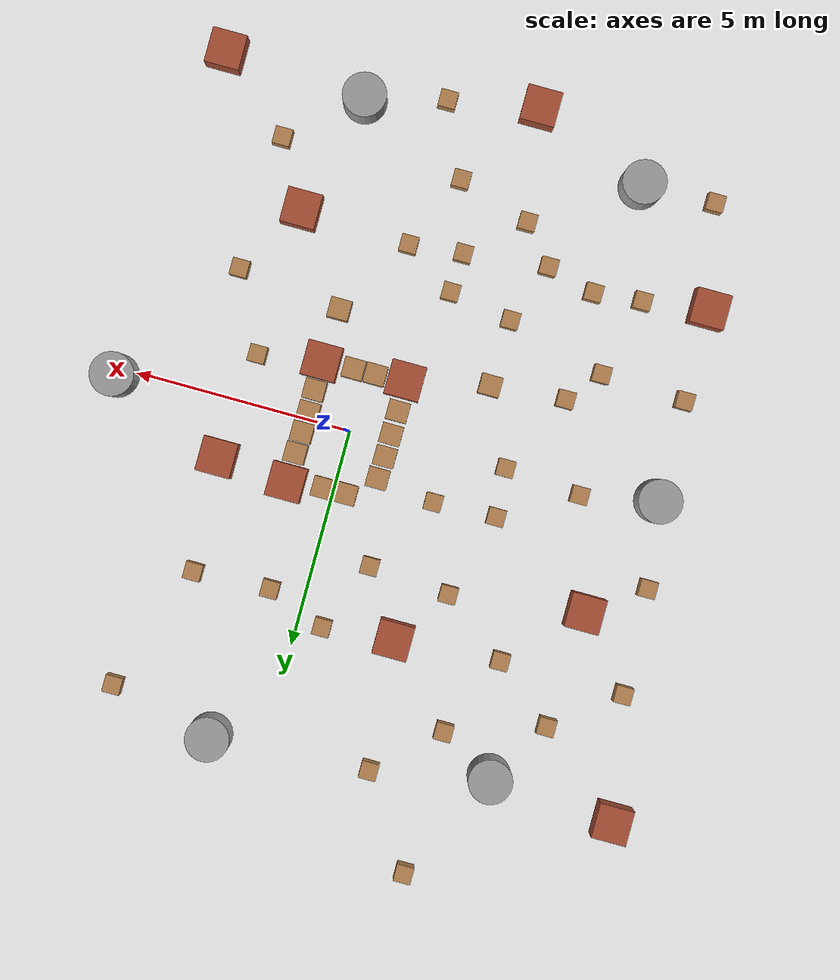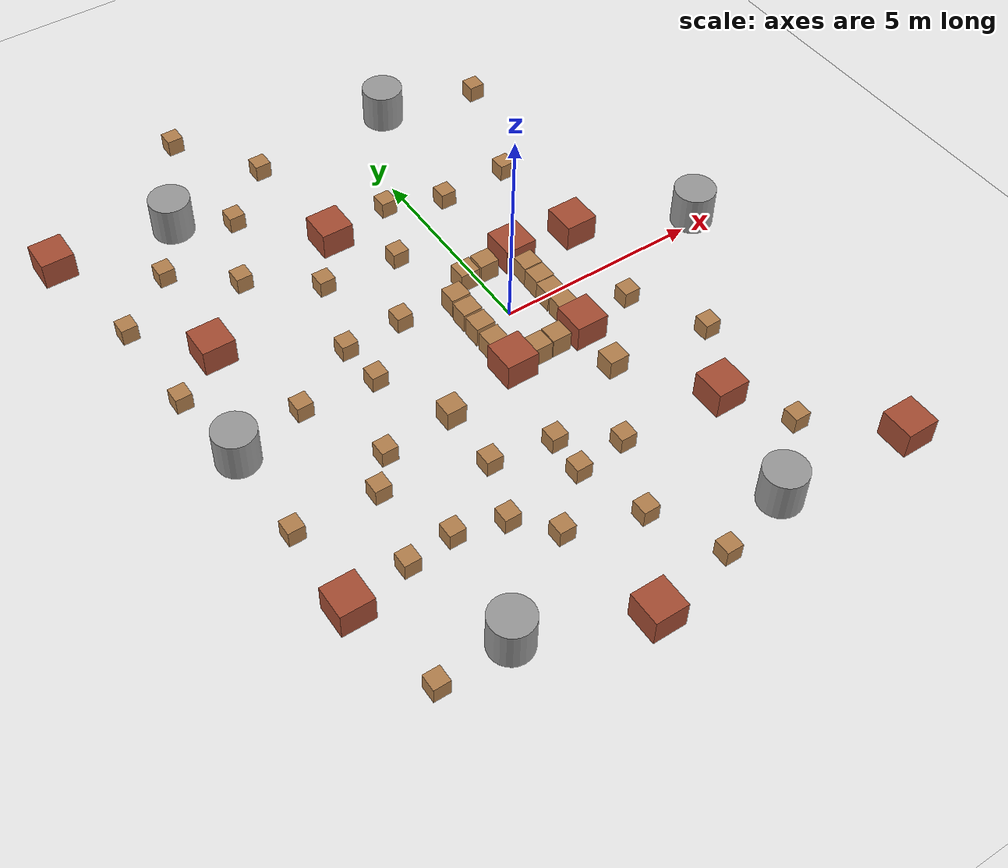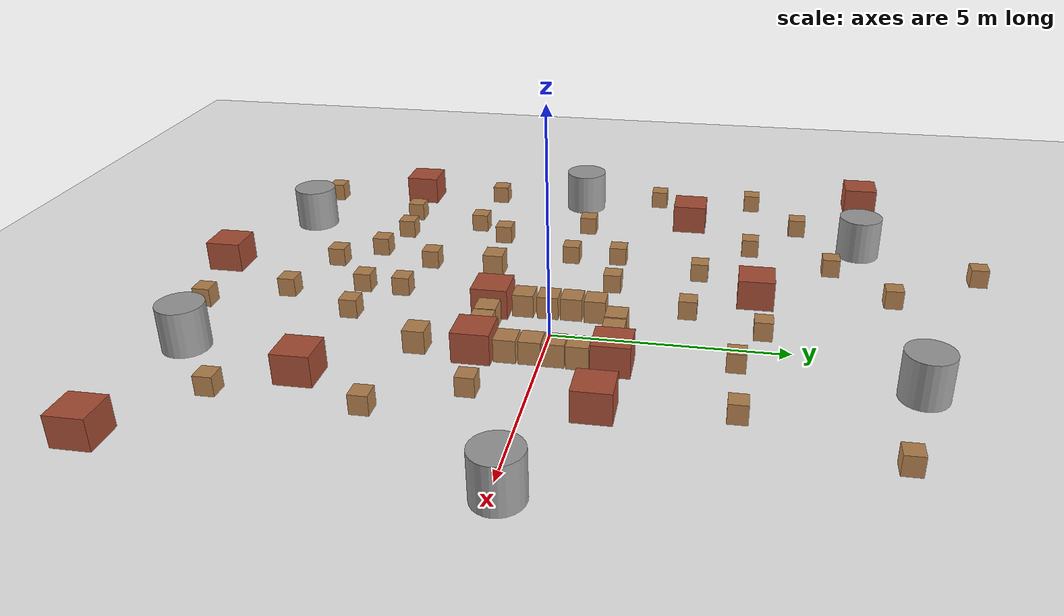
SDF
<sdf version="1.6">
 <world name="default">
  <light name="sun" type="directional">
   <pose>0 0 10 0 -0 0</pose>
   <diffuse>0.8 0.8 0.8 1</diffuse>
   <specular>0.1 0.1 0.1 1</specular>
   <attenuation>
    <range>1000</range>
    <constant>0.9</constant>
    <linear>0.01</linear>
    <quadratic>0.001</quadratic>
   </attenuation>
   <direction>-0.5 0.5 -1</direction>
  </light>
  <model name="ground_plane">
   <static>1</static>
   <link name="link">
    <collision name="collision">
     <geometry><plane><normal>0 0 1</normal><size>100 100</size></plane></geometry>
     <surface><friction><ode><mu>100</mu><mu2>50</mu2></ode></friction></surface>
    </collision>
    <visual name="visual">
     <cast_shadows>0</cast_shadows>
     <geometry><plane><normal>0 0 1</normal><size>100 100</size></plane></geometry>
     <material>
      <script><uri>file://media/materials/scripts/gazebo.material</uri><name>Gazebo/White</name></script>
     </material>
    </visual>
   </link>
  </model>
  <gravity>0 0 -9.8</gravity>
  <magnetic_field>6e-06 2.3e-05 -4.2e-05</magnetic_field>
  <atmosphere type="adiabatic"/>
  <physics name="default_physics" default="0" type="ode">
   <max_step_size>0.005</max_step_size>
   <real_time_factor>1</real_time_factor>
   <real_time_update_rate>1000</real_time_update_rate>
  </physics>
  <scene><ambient>0.4 0.4 0.4 1</ambient><background>0.7 0.7 0.7 1</background><shadows>1</shadows></scene>
  <spherical_coordinates>
   <surface_model>EARTH_WGS84</surface_model>
   <latitude_deg>0</latitude_deg>
   <longitude_deg>0</longitude_deg>
   <elevation>0</elevation>
   <heading_deg>0</heading_deg>
  </spherical_coordinates>
  <model name="HeavyBox_2">
   <link name="link">
    <inertial>
     <mass>2</mass>
     <inertia>
      <ixx>0.0402452</ixx>
      <ixy>0</ixy>
      <ixz>0</ixz>
      <iyy>0.0399236</iyy>
      <iyz>0</iyz>
      <izz>0.0461707</izz>
     </inertia>
    </inertial>
    <visual name="visual">
     <geometry><box><size>0.79482 0.800386 0.684447</size></box></geometry>
     <material>
      <script><name>Gazebo/Bricks</name><uri>file://media/materials/scripts/gazebo.material</uri></script>
      <ambient>0.3 0.3 0.3 1</ambient>
      <diffuse>0.7 0.7 0.7 1</diffuse>
      <specular>0.01 0.01 0.01 1</specular>
      <emissive>0 0 0 1</emissive>
     </material>
    </visual>
    <collision name="collision">
     <geometry><box><size>0.79482 0.800386 0.684447</size></box></geometry>
     <surface>
      <friction>
       <ode><mu>1</mu><mu2>1</mu2><fdir1>0 0 0</fdir1><slip1>0</slip1><slip2>0</slip2></ode>
       <torsional>
        <coefficient>1</coefficient>
        <patch_radius>0</patch_radius>
        <surface_radius>0</surface_radius>
        <use_patch_radius>1</use_patch_radius>
        <ode><slip>0</slip></ode>
       </torsional>
      </friction>
      <bounce><restitution_coefficient>0</restitution_coefficient><threshold>1e+06</threshold></bounce>
      <contact>
       <collide_without_contact>0</collide_without_contact>
       <collide_without_contact_bitmask>1</collide_without_contact_bitmask>
       <collide_bitmask>1</collide_bitmask>
       <ode>
        <soft_cfm>0</soft_cfm>
        <soft_erp>0.2</soft_erp>
        <kp>1e+13</kp>
        <kd>1</kd>
        <max_vel>0.01</max_vel>
        <min_depth>0</min_depth>
       </ode>
       <bullet>
        <split_impulse>1</split_impulse>
        <split_impulse_penetration_threshold>-0.01</split_impulse_penetration_threshold>
        <soft_cfm>0</soft_cfm>
        <soft_erp>0.2</soft_erp>
        <kp>1e+13</kp>
        <kd>1</kd>
       </bullet>
      </contact>
     </surface>
    </collision>
   </link>
   <static>0</static>
   <pose>-0.910015 -1.43287 0.342219 -1.2e-05 -0 -5.8e-05</pose>
  </model>
  <model name="Box_0">
   <link name="link">
    <inertial>
     <mass>0.01</mass>
     <inertia>
      <ixx>0.00455697</ixx>
      <ixy>0</ixy>
      <ixz>0</ixz>
      <iyy>0.00475558</iyy>
      <iyz>0</iyz>
      <izz>0.00426137</izz>
     </inertia>
    </inertial>
    <visual name="visual">
     <geometry><box><size>0.483208 0.461193 0.514245</size></box></geometry>
     <material>
      <script><name>Gazebo/WoodFloor</name><uri>file://media/materials/scripts/gazebo.material</uri></script>
      <ambient>0.3 0.3 0.3 1</ambient>
      <diffuse>0.7 0.7 0.7 1</diffuse>
      <specular>0.01 0.01 0.01 1</specular>
      <emissive>0 0 0 1</emissive>
     </material>
    </visual>
    <collision name="collision">
     <geometry><box><size>0.483208 0.461193 0.514245</size></box></geometry>
     <surface>
      <friction>
       <ode><mu>1</mu><mu2>1</mu2><fdir1>0 0 0</fdir1><slip1>0</slip1><slip2>0</slip2></ode>
       <torsional>
        <coefficient>1</coefficient>
        <patch_radius>0</patch_radius>
        <surface_radius>0</surface_radius>
        <use_patch_radius>1</use_patch_radius>
        <ode><slip>0</slip></ode>
       </torsional>
      </friction>
      <bounce><restitution_coefficient>0</restitution_coefficient><threshold>1e+06</threshold></bounce>
      <contact>
       <collide_without_contact>0</collide_without_contact>
       <collide_without_contact_bitmask>1</collide_without_contact_bitmask>
       <collide_bitmask>1</collide_bitmask>
       <ode>
        <soft_cfm>0</soft_cfm>
        <soft_erp>0.2</soft_erp>
        <kp>1e+13</kp>
        <kd>1</kd>
        <max_vel>0.01</max_vel>
        <min_depth>0</min_depth>
       </ode>
       <bullet>
        <split_impulse>1</split_impulse>
        <split_impulse_penetration_threshold>-0.01</split_impulse_penetration_threshold>
        <soft_cfm>0</soft_cfm>
        <soft_erp>0.2</soft_erp>
        <kp>1e+13</kp>
        <kd>1</kd>
       </bullet>
      </contact>
     </surface>
    </collision>
   </link>
   <static>0</static>
   <pose>-0.9238 -0.184873 0.257122 0 -0 0</pose>
  </model>
  <model name="Box_1">
   <link name="link">
    <inertial>
     <mass>0.01</mass>
     <inertia>
      <ixx>0.00455697</ixx>
      <ixy>0</ixy>
      <ixz>0</ixz>
      <iyy>0.00475558</iyy>
      <iyz>0</iyz>
      <izz>0.00426137</izz>
     </inertia>
    </inertial>
    <visual name="visual">
     <geometry><box><size>0.483208 0.461193 0.514245</size></box></geometry>
     <material>
      <script><name>Gazebo/WoodFloor</name><uri>file://media/materials/scripts/gazebo.material</uri></script>
      <ambient>0.3 0.3 0.3 1</ambient>
      <diffuse>0.7 0.7 0.7 1</diffuse>
      <specular>0.01 0.01 0.01 1</specular>
      <emissive>0 0 0 1</emissive>
     </material>
    </visual>
    <collision name="collision">
     <geometry><box><size>0.483208 0.461193 0.514245</size></box></geometry>
     <surface>
      <friction>
       <ode><mu>1</mu><mu2>1</mu2><fdir1>0 0 0</fdir1><slip1>0</slip1><slip2>0</slip2></ode>
       <torsional>
        <coefficient>1</coefficient>
        <patch_radius>0</patch_radius>
        <surface_radius>0</surface_radius>
        <use_patch_radius>1</use_patch_radius>
        <ode><slip>0</slip></ode>
       </torsional>
      </friction>
      <bounce><restitution_coefficient>0</restitution_coefficient><threshold>1e+06</threshold></bounce>
      <contact>
       <collide_without_contact>0</collide_without_contact>
       <collide_without_contact_bitmask>1</collide_without_contact_bitmask>
       <collide_bitmask>1</collide_bitmask>
       <ode>
        <soft_cfm>0</soft_cfm>
        <soft_erp>0.2</soft_erp>
        <kp>1e+13</kp>
        <kd>1</kd>
        <max_vel>0.01</max_vel>
        <min_depth>0</min_depth>
       </ode>
       <bullet>
        <split_impulse>1</split_impulse>
        <split_impulse_penetration_threshold>-0.01</split_impulse_penetration_threshold>
        <soft_cfm>0</soft_cfm>
        <soft_erp>0.2</soft_erp>
        <kp>1e+13</kp>
        <kd>1</kd>
       </bullet>
      </contact>
     </surface>
    </collision>
   </link>
   <static>0</static>
   <pose>-0.922789 0.329549 0.257122 0 -0 0</pose>
  </model>
  <model name="Box_2">
   <link name="link">
    <inertial>
     <mass>0.01</mass>
     <inertia>
      <ixx>0.00455697</ixx>
      <ixy>0</ixy>
      <ixz>0</ixz>
      <iyy>0.00475558</iyy>
      <iyz>0</iyz>
      <izz>0.00426137</izz>
     </inertia>
    </inertial>
    <visual name="visual">
     <geometry><box><size>0.483208 0.461193 0.514245</size></box></geometry>
     <material>
      <script><name>Gazebo/WoodFloor</name><uri>file://media/materials/scripts/gazebo.material</uri></script>
      <ambient>0.3 0.3 0.3 1</ambient>
      <diffuse>0.7 0.7 0.7 1</diffuse>
      <specular>0.01 0.01 0.01 1</specular>
      <emissive>0 0 0 1</emissive>
     </material>
    </visual>
    <collision name="collision">
     <geometry><box><size>0.483208 0.461193 0.514245</size></box></geometry>
     <surface>
      <friction>
       <ode><mu>1</mu><mu2>1</mu2><fdir1>0 0 0</fdir1><slip1>0</slip1><slip2>0</slip2></ode>
       <torsional>
        <coefficient>1</coefficient>
        <patch_radius>0</patch_radius>
        <surface_radius>0</surface_radius>
        <use_patch_radius>1</use_patch_radius>
        <ode><slip>0</slip></ode>
       </torsional>
      </friction>
      <bounce><restitution_coefficient>0</restitution_coefficient><threshold>1e+06</threshold></bounce>
      <contact>
       <collide_without_contact>0</collide_without_contact>
       <collide_without_contact_bitmask>1</collide_without_contact_bitmask>
       <collide_bitmask>1</collide_bitmask>
       <ode>
        <soft_cfm>0</soft_cfm>
        <soft_erp>0.2</soft_erp>
        <kp>1e+13</kp>
        <kd>1</kd>
        <max_vel>0.01</max_vel>
        <min_depth>0</min_depth>
       </ode>
       <bullet>
        <split_impulse>1</split_impulse>
        <split_impulse_penetration_threshold>-0.01</split_impulse_penetration_threshold>
        <soft_cfm>0</soft_cfm>
        <soft_erp>0.2</soft_erp>
        <kp>1e+13</kp>
        <kd>1</kd>
       </bullet>
      </contact>
     </surface>
    </collision>
   </link>
   <static>0</static>
   <pose>-0.892794 0.843712 0.257122 0 -0 0</pose>
  </model>
  <model name="Box_4">
   <link name="link">
    <inertial>
     <mass>0.01</mass>
     <inertia>
      <ixx>0.00455697</ixx>
      <ixy>0</ixy>
      <ixz>0</ixz>
      <iyy>0.00475558</iyy>
      <iyz>0</iyz>
      <izz>0.00426137</izz>
     </inertia>
    </inertial>
    <visual name="visual">
     <geometry><box><size>0.483208 0.461193 0.514245</size></box></geometry>
     <material>
      <script><name>Gazebo/WoodFloor</name><uri>file://media/materials/scripts/gazebo.material</uri></script>
      <ambient>0.3 0.3 0.3 1</ambient>
      <diffuse>0.7 0.7 0.7 1</diffuse>
      <specular>0.01 0.01 0.01 1</specular>
      <emissive>0 0 0 1</emissive>
     </material>
    </visual>
    <collision name="collision">
     <geometry><box><size>0.483208 0.461193 0.514245</size></box></geometry>
     <surface>
      <friction>
       <ode><mu>1</mu><mu2>1</mu2><fdir1>0 0 0</fdir1><slip1>0</slip1><slip2>0</slip2></ode>
       <torsional>
        <coefficient>1</coefficient>
        <patch_radius>0</patch_radius>
        <surface_radius>0</surface_radius>
        <use_patch_radius>1</use_patch_radius>
        <ode><slip>0</slip></ode>
       </torsional>
      </friction>
      <bounce><restitution_coefficient>0</restitution_coefficient><threshold>1e+06</threshold></bounce>
      <contact>
       <collide_without_contact>0</collide_without_contact>
       <collide_without_contact_bitmask>1</collide_without_contact_bitmask>
       <collide_bitmask>1</collide_bitmask>
       <ode>
        <soft_cfm>0</soft_cfm>
        <soft_erp>0.2</soft_erp>
        <kp>1e+13</kp>
        <kd>1</kd>
        <max_vel>0.01</max_vel>
        <min_depth>0</min_depth>
       </ode>
       <bullet>
        <split_impulse>1</split_impulse>
        <split_impulse_penetration_threshold>-0.01</split_impulse_penetration_threshold>
        <soft_cfm>0</soft_cfm>
        <soft_erp>0.2</soft_erp>
        <kp>1e+13</kp>
        <kd>1</kd>
       </bullet>
      </contact>
     </surface>
    </collision>
   </link>
   <static>0</static>
   <pose>-0.227566 -1.38976 0.257122 0 0 -2.9e-05</pose>
  </model>
  <model name="Box_5">
   <link name="link">
    <inertial>
     <mass>0.01</mass>
     <inertia>
      <ixx>0.00455697</ixx>
      <ixy>0</ixy>
      <ixz>0</ixz>
      <iyy>0.00475558</iyy>
      <iyz>0</iyz>
      <izz>0.00426137</izz>
     </inertia>
    </inertial>
    <visual name="visual">
     <geometry><box><size>0.483208 0.461193 0.514245</size></box></geometry>
     <material>
      <script><name>Gazebo/WoodFloor</name><uri>file://media/materials/scripts/gazebo.material</uri></script>
      <ambient>0.3 0.3 0.3 1</ambient>
      <diffuse>0.7 0.7 0.7 1</diffuse>
      <specular>0.01 0.01 0.01 1</specular>
      <emissive>0 0 0 1</emissive>
     </material>
    </visual>
    <collision name="collision">
     <geometry><box><size>0.483208 0.461193 0.514245</size></box></geometry>
     <surface>
      <friction>
       <ode><mu>1</mu><mu2>1</mu2><fdir1>0 0 0</fdir1><slip1>0</slip1><slip2>0</slip2></ode>
       <torsional>
        <coefficient>1</coefficient>
        <patch_radius>0</patch_radius>
        <surface_radius>0</surface_radius>
        <use_patch_radius>1</use_patch_radius>
        <ode><slip>0</slip></ode>
       </torsional>
      </friction>
      <bounce><restitution_coefficient>0</restitution_coefficient><threshold>1e+06</threshold></bounce>
      <contact>
       <collide_without_contact>0</collide_without_contact>
       <collide_without_contact_bitmask>1</collide_without_contact_bitmask>
       <collide_bitmask>1</collide_bitmask>
       <ode>
        <soft_cfm>0</soft_cfm>
        <soft_erp>0.2</soft_erp>
        <kp>1e+13</kp>
        <kd>1</kd>
        <max_vel>0.01</max_vel>
        <min_depth>0</min_depth>
       </ode>
       <bullet>
        <split_impulse>1</split_impulse>
        <split_impulse_penetration_threshold>-0.01</split_impulse_penetration_threshold>
        <soft_cfm>0</soft_cfm>
        <soft_erp>0.2</soft_erp>
        <kp>1e+13</kp>
        <kd>1</kd>
       </bullet>
      </contact>
     </surface>
    </collision>
   </link>
   <static>0</static>
   <pose>0.279819 -1.3846 0.257122 0 0 -2.4e-05</pose>
  </model>
  <model name="HeavyBox_3">
   <link name="link">
    <inertial>
     <mass>2</mass>
     <inertia>
      <ixx>0.0402452</ixx>
      <ixy>0</ixy>
      <ixz>0</ixz>
      <iyy>0.0399236</iyy>
      <iyz>0</iyz>
      <izz>0.0461707</izz>
     </inertia>
    </inertial>
    <visual name="visual">
     <geometry><box><size>0.79482 0.800386 0.684447</size></box></geometry>
     <material>
      <script><name>Gazebo/Bricks</name><uri>file://media/materials/scripts/gazebo.material</uri></script>
      <ambient>0.3 0.3 0.3 1</ambient>
      <diffuse>0.7 0.7 0.7 1</diffuse>
      <specular>0.01 0.01 0.01 1</specular>
      <emissive>0 0 0 1</emissive>
     </material>
    </visual>
    <collision name="collision">
     <geometry><box><size>0.79482 0.800386 0.684447</size></box></geometry>
     <surface>
      <friction>
       <ode><mu>1</mu><mu2>1</mu2><fdir1>0 0 0</fdir1><slip1>0</slip1><slip2>0</slip2></ode>
       <torsional>
        <coefficient>1</coefficient>
        <patch_radius>0</patch_radius>
        <surface_radius>0</surface_radius>
        <use_patch_radius>1</use_patch_radius>
        <ode><slip>0</slip></ode>
       </torsional>
      </friction>
      <bounce><restitution_coefficient>0</restitution_coefficient><threshold>1e+06</threshold></bounce>
      <contact>
       <collide_without_contact>0</collide_without_contact>
       <collide_without_contact_bitmask>1</collide_without_contact_bitmask>
       <collide_bitmask>1</collide_bitmask>
       <ode>
        <soft_cfm>0</soft_cfm>
        <soft_erp>0.2</soft_erp>
        <kp>1e+13</kp>
        <kd>1</kd>
        <max_vel>0.01</max_vel>
        <min_depth>0</min_depth>
       </ode>
       <bullet>
        <split_impulse>1</split_impulse>
        <split_impulse_penetration_threshold>-0.01</split_impulse_penetration_threshold>
        <soft_cfm>0</soft_cfm>
        <soft_erp>0.2</soft_erp>
        <kp>1e+13</kp>
        <kd>1</kd>
       </bullet>
      </contact>
     </surface>
    </collision>
   </link>
   <static>0</static>
   <pose>1.0079 -1.3546 0.342219 1.2e-05 -0 3.4e-05</pose>
  </model>
  <model name="Box_6">
   <link name="link">
    <inertial>
     <mass>0.01</mass>
     <inertia>
      <ixx>0.00455697</ixx>
      <ixy>0</ixy>
      <ixz>0</ixz>
      <iyy>0.00475558</iyy>
      <iyz>0</iyz>
      <izz>0.00426137</izz>
     </inertia>
    </inertial>
    <visual name="visual">
     <geometry><box><size>0.483208 0.461193 0.514245</size></box></geometry>
     <material>
      <script><name>Gazebo/WoodFloor</name><uri>file://media/materials/scripts/gazebo.material</uri></script>
      <ambient>0.3 0.3 0.3 1</ambient>
      <diffuse>0.7 0.7 0.7 1</diffuse>
      <specular>0.01 0.01 0.01 1</specular>
      <emissive>0 0 0 1</emissive>
     </material>
    </visual>
    <collision name="collision">
     <geometry><box><size>0.483208 0.461193 0.514245</size></box></geometry>
     <surface>
      <friction>
       <ode><mu>1</mu><mu2>1</mu2><fdir1>0 0 0</fdir1><slip1>0</slip1><slip2>0</slip2></ode>
       <torsional>
        <coefficient>1</coefficient>
        <patch_radius>0</patch_radius>
        <surface_radius>0</surface_radius>
        <use_patch_radius>1</use_patch_radius>
        <ode><slip>0</slip></ode>
       </torsional>
      </friction>
      <bounce><restitution_coefficient>0</restitution_coefficient><threshold>1e+06</threshold></bounce>
      <contact>
       <collide_without_contact>0</collide_without_contact>
       <collide_without_contact_bitmask>1</collide_without_contact_bitmask>
       <collide_bitmask>1</collide_bitmask>
       <ode>
        <soft_cfm>0</soft_cfm>
        <soft_erp>0.2</soft_erp>
        <kp>1e+13</kp>
        <kd>1</kd>
        <max_vel>0.01</max_vel>
        <min_depth>0</min_depth>
       </ode>
       <bullet>
        <split_impulse>1</split_impulse>
        <split_impulse_penetration_threshold>-0.01</split_impulse_penetration_threshold>
        <soft_cfm>0</soft_cfm>
        <soft_erp>0.2</soft_erp>
        <kp>1e+13</kp>
        <kd>1</kd>
       </bullet>
      </contact>
     </surface>
    </collision>
   </link>
   <static>0</static>
   <pose>1.00077 -0.692545 0.257122 0 -0 0</pose>
  </model>
  <model name="Box_7">
   <link name="link">
    <inertial>
     <mass>0.01</mass>
     <inertia>
      <ixx>0.00455697</ixx>
      <ixy>0</ixy>
      <ixz>0</ixz>
      <iyy>0.00475558</iyy>
      <iyz>0</iyz>
      <izz>0.00426137</izz>
     </inertia>
    </inertial>
    <visual name="visual">
     <geometry><box><size>0.483208 0.461193 0.514245</size></box></geometry>
     <material>
      <script><name>Gazebo/WoodFloor</name><uri>file://media/materials/scripts/gazebo.material</uri></script>
      <ambient>0.3 0.3 0.3 1</ambient>
      <diffuse>0.7 0.7 0.7 1</diffuse>
      <specular>0.01 0.01 0.01 1</specular>
      <emissive>0 0 0 1</emissive>
     </material>
    </visual>
    <collision name="collision">
     <geometry><box><size>0.483208 0.461193 0.514245</size></box></geometry>
     <surface>
      <friction>
       <ode><mu>1</mu><mu2>1</mu2><fdir1>0 0 0</fdir1><slip1>0</slip1><slip2>0</slip2></ode>
       <torsional>
        <coefficient>1</coefficient>
        <patch_radius>0</patch_radius>
        <surface_radius>0</surface_radius>
        <use_patch_radius>1</use_patch_radius>
        <ode><slip>0</slip></ode>
       </torsional>
      </friction>
      <bounce><restitution_coefficient>0</restitution_coefficient><threshold>1e+06</threshold></bounce>
      <contact>
       <collide_without_contact>0</collide_without_contact>
       <collide_without_contact_bitmask>1</collide_without_contact_bitmask>
       <collide_bitmask>1</collide_bitmask>
       <ode>
        <soft_cfm>0</soft_cfm>
        <soft_erp>0.2</soft_erp>
        <kp>1e+13</kp>
        <kd>1</kd>
        <max_vel>0.01</max_vel>
        <min_depth>0</min_depth>
       </ode>
       <bullet>
        <split_impulse>1</split_impulse>
        <split_impulse_penetration_threshold>-0.01</split_impulse_penetration_threshold>
        <soft_cfm>0</soft_cfm>
        <soft_erp>0.2</soft_erp>
        <kp>1e+13</kp>
        <kd>1</kd>
       </bullet>
      </contact>
     </surface>
    </collision>
   </link>
   <static>0</static>
   <pose>1.01776 0.295686 0.257122 0 -0 1e-06</pose>
  </model>
  <model name="Box_8">
   <link name="link">
    <inertial>
     <mass>0.01</mass>
     <inertia>
      <ixx>0.00455697</ixx>
      <ixy>0</ixy>
      <ixz>0</ixz>
      <iyy>0.00475558</iyy>
      <iyz>0</iyz>
      <izz>0.00426137</izz>
     </inertia>
    </inertial>
    <visual name="visual">
     <geometry><box><size>0.483208 0.461193 0.514245</size></box></geometry>
     <material>
      <script><name>Gazebo/WoodFloor</name><uri>file://media/materials/scripts/gazebo.material</uri></script>
      <ambient>0.3 0.3 0.3 1</ambient>
      <diffuse>0.7 0.7 0.7 1</diffuse>
      <specular>0.01 0.01 0.01 1</specular>
      <emissive>0 0 0 1</emissive>
     </material>
    </visual>
    <collision name="collision">
     <geometry><box><size>0.483208 0.461193 0.514245</size></box></geometry>
     <surface>
      <friction>
       <ode><mu>1</mu><mu2>1</mu2><fdir1>0 0 0</fdir1><slip1>0</slip1><slip2>0</slip2></ode>
       <torsional>
        <coefficient>1</coefficient>
        <patch_radius>0</patch_radius>
        <surface_radius>0</surface_radius>
        <use_patch_radius>1</use_patch_radius>
        <ode><slip>0</slip></ode>
       </torsional>
      </friction>
      <bounce><restitution_coefficient>0</restitution_coefficient><threshold>1e+06</threshold></bounce>
      <contact>
       <collide_without_contact>0</collide_without_contact>
       <collide_without_contact_bitmask>1</collide_without_contact_bitmask>
       <collide_bitmask>1</collide_bitmask>
       <ode>
        <soft_cfm>0</soft_cfm>
        <soft_erp>0.2</soft_erp>
        <kp>1e+13</kp>
        <kd>1</kd>
        <max_vel>0.01</max_vel>
        <min_depth>0</min_depth>
       </ode>
       <bullet>
        <split_impulse>1</split_impulse>
        <split_impulse_penetration_threshold>-0.01</split_impulse_penetration_threshold>
        <soft_cfm>0</soft_cfm>
        <soft_erp>0.2</soft_erp>
        <kp>1e+13</kp>
        <kd>1</kd>
       </bullet>
      </contact>
     </surface>
    </collision>
   </link>
   <static>0</static>
   <pose>1.00187 -0.183727 0.257122 0 -0 1e-06</pose>
  </model>
  <model name="HeavyBox_4">
   <link name="link">
    <inertial>
     <mass>2</mass>
     <inertia>
      <ixx>0.0402452</ixx>
      <ixy>0</ixy>
      <ixz>0</ixz>
      <iyy>0.0399236</iyy>
      <iyz>0</iyz>
      <izz>0.0461707</izz>
     </inertia>
    </inertial>
    <visual name="visual">
     <geometry><box><size>0.79482 0.800386 0.684447</size></box></geometry>
     <material>
      <script><name>Gazebo/Bricks</name><uri>file://media/materials/scripts/gazebo.material</uri></script>
      <ambient>0.3 0.3 0.3 1</ambient>
      <diffuse>0.7 0.7 0.7 1</diffuse>
      <specular>0.01 0.01 0.01 1</specular>
      <emissive>0 0 0 1</emissive>
     </material>
    </visual>
    <collision name="collision">
     <geometry><box><size>0.79482 0.800386 0.684447</size></box></geometry>
     <surface>
      <friction>
       <ode><mu>1</mu><mu2>1</mu2><fdir1>0 0 0</fdir1><slip1>0</slip1><slip2>0</slip2></ode>
       <torsional>
        <coefficient>1</coefficient>
        <patch_radius>0</patch_radius>
        <surface_radius>0</surface_radius>
        <use_patch_radius>1</use_patch_radius>
        <ode><slip>0</slip></ode>
       </torsional>
      </friction>
      <bounce><restitution_coefficient>0</restitution_coefficient><threshold>1e+06</threshold></bounce>
      <contact>
       <collide_without_contact>0</collide_without_contact>
       <collide_without_contact_bitmask>1</collide_without_contact_bitmask>
       <collide_bitmask>1</collide_bitmask>
       <ode>
        <soft_cfm>0</soft_cfm>
        <soft_erp>0.2</soft_erp>
        <kp>1e+13</kp>
        <kd>1</kd>
        <max_vel>0.01</max_vel>
        <min_depth>0</min_depth>
       </ode>
       <bullet>
        <split_impulse>1</split_impulse>
        <split_impulse_penetration_threshold>-0.01</split_impulse_penetration_threshold>
        <soft_cfm>0</soft_cfm>
        <soft_erp>0.2</soft_erp>
        <kp>1e+13</kp>
        <kd>1</kd>
       </bullet>
      </contact>
     </surface>
    </collision>
   </link>
   <static>0</static>
   <pose>1.05426 1.46286 0.342219 -1.2e-05 -0 2.3e-05</pose>
  </model>
  <model name="Box_9">
   <link name="link">
    <inertial>
     <mass>0.01</mass>
     <inertia>
      <ixx>0.00455697</ixx>
      <ixy>0</ixy>
      <ixz>0</ixz>
      <iyy>0.00475558</iyy>
      <iyz>0</iyz>
      <izz>0.00426137</izz>
     </inertia>
    </inertial>
    <visual name="visual">
     <geometry><box><size>0.483208 0.461193 0.514245</size></box></geometry>
     <material>
      <script><name>Gazebo/WoodFloor</name><uri>file://media/materials/scripts/gazebo.material</uri></script>
      <ambient>0.3 0.3 0.3 1</ambient>
      <diffuse>0.7 0.7 0.7 1</diffuse>
      <specular>0.01 0.01 0.01 1</specular>
      <emissive>0 0 0 1</emissive>
     </material>
    </visual>
    <collision name="collision">
     <geometry><box><size>0.483208 0.461193 0.514245</size></box></geometry>
     <surface>
      <friction>
       <ode><mu>1</mu><mu2>1</mu2><fdir1>0 0 0</fdir1><slip1>0</slip1><slip2>0</slip2></ode>
       <torsional>
        <coefficient>1</coefficient>
        <patch_radius>0</patch_radius>
        <surface_radius>0</surface_radius>
        <use_patch_radius>1</use_patch_radius>
        <ode><slip>0</slip></ode>
       </torsional>
      </friction>
      <bounce><restitution_coefficient>0</restitution_coefficient><threshold>1e+06</threshold></bounce>
      <contact>
       <collide_without_contact>0</collide_without_contact>
       <collide_without_contact_bitmask>1</collide_without_contact_bitmask>
       <collide_bitmask>1</collide_bitmask>
       <ode>
        <soft_cfm>0</soft_cfm>
        <soft_erp>0.2</soft_erp>
        <kp>1e+13</kp>
        <kd>1</kd>
        <max_vel>0.01</max_vel>
        <min_depth>0</min_depth>
       </ode>
       <bullet>
        <split_impulse>1</split_impulse>
        <split_impulse_penetration_threshold>-0.01</split_impulse_penetration_threshold>
        <soft_cfm>0</soft_cfm>
        <soft_erp>0.2</soft_erp>
        <kp>1e+13</kp>
        <kd>1</kd>
       </bullet>
      </contact>
     </surface>
    </collision>
   </link>
   <static>0</static>
   <pose>-0.297671 1.36802 0.257122 0 -0 0</pose>
  </model>
  <model name="Box_10">
   <link name="link">
    <inertial>
     <mass>0.01</mass>
     <inertia>
      <ixx>0.00455697</ixx>
      <ixy>0</ixy>
      <ixz>0</ixz>
      <iyy>0.00475558</iyy>
      <iyz>0</iyz>
      <izz>0.00426137</izz>
     </inertia>
    </inertial>
    <visual name="visual">
     <geometry><box><size>0.483208 0.461193 0.514245</size></box></geometry>
     <material>
      <script><name>Gazebo/WoodFloor</name><uri>file://media/materials/scripts/gazebo.material</uri></script>
      <ambient>0.3 0.3 0.3 1</ambient>
      <diffuse>0.7 0.7 0.7 1</diffuse>
      <specular>0.01 0.01 0.01 1</specular>
      <emissive>0 0 0 1</emissive>
     </material>
    </visual>
    <collision name="collision">
     <geometry><box><size>0.483208 0.461193 0.514245</size></box></geometry>
     <surface>
      <friction>
       <ode><mu>1</mu><mu2>1</mu2><fdir1>0 0 0</fdir1><slip1>0</slip1><slip2>0</slip2></ode>
       <torsional>
        <coefficient>1</coefficient>
        <patch_radius>0</patch_radius>
        <surface_radius>0</surface_radius>
        <use_patch_radius>1</use_patch_radius>
        <ode><slip>0</slip></ode>
       </torsional>
      </friction>
      <bounce><restitution_coefficient>0</restitution_coefficient><threshold>1e+06</threshold></bounce>
      <contact>
       <collide_without_contact>0</collide_without_contact>
       <collide_without_contact_bitmask>1</collide_without_contact_bitmask>
       <collide_bitmask>1</collide_bitmask>
       <ode>
        <soft_cfm>0</soft_cfm>
        <soft_erp>0.2</soft_erp>
        <kp>1e+13</kp>
        <kd>1</kd>
        <max_vel>0.01</max_vel>
        <min_depth>0</min_depth>
       </ode>
       <bullet>
        <split_impulse>1</split_impulse>
        <split_impulse_penetration_threshold>-0.01</split_impulse_penetration_threshold>
        <soft_cfm>0</soft_cfm>
        <soft_erp>0.2</soft_erp>
        <kp>1e+13</kp>
        <kd>1</kd>
       </bullet>
      </contact>
     </surface>
    </collision>
   </link>
   <static>0</static>
   <pose>0.235099 1.37485 0.257122 0 -0 0</pose>
  </model>
  <model name="Box_11">
   <link name="link">
    <inertial>
     <mass>0.01</mass>
     <inertia>
      <ixx>0.00455697</ixx>
      <ixy>0</ixy>
      <ixz>0</ixz>
      <iyy>0.00475558</iyy>
      <iyz>0</iyz>
      <izz>0.00426137</izz>
     </inertia>
    </inertial>
    <visual name="visual">
     <geometry><box><size>0.483208 0.461193 0.514245</size></box></geometry>
     <material>
      <script><name>Gazebo/WoodFloor</name><uri>file://media/materials/scripts/gazebo.material</uri></script>
      <ambient>0.3 0.3 0.3 1</ambient>
      <diffuse>0.7 0.7 0.7 1</diffuse>
      <specular>0.01 0.01 0.01 1</specular>
      <emissive>0 0 0 1</emissive>
     </material>
    </visual>
    <collision name="collision">
     <geometry><box><size>0.483208 0.461193 0.514245</size></box></geometry>
     <surface>
      <friction>
       <ode><mu>1</mu><mu2>1</mu2><fdir1>0 0 0</fdir1><slip1>0</slip1><slip2>0</slip2></ode>
       <torsional>
        <coefficient>1</coefficient>
        <patch_radius>0</patch_radius>
        <surface_radius>0</surface_radius>
        <use_patch_radius>1</use_patch_radius>
        <ode><slip>0</slip></ode>
       </torsional>
      </friction>
      <bounce><restitution_coefficient>0</restitution_coefficient><threshold>1e+06</threshold></bounce>
      <contact>
       <collide_without_contact>0</collide_without_contact>
       <collide_without_contact_bitmask>1</collide_without_contact_bitmask>
       <collide_bitmask>1</collide_bitmask>
       <ode>
        <soft_cfm>0</soft_cfm>
        <soft_erp>0.2</soft_erp>
        <kp>1e+13</kp>
        <kd>1</kd>
        <max_vel>0.01</max_vel>
        <min_depth>0</min_depth>
       </ode>
       <bullet>
        <split_impulse>1</split_impulse>
        <split_impulse_penetration_threshold>-0.01</split_impulse_penetration_threshold>
        <soft_cfm>0</soft_cfm>
        <soft_erp>0.2</soft_erp>
        <kp>1e+13</kp>
        <kd>1</kd>
       </bullet>
      </contact>
     </surface>
    </collision>
   </link>
   <static>0</static>
   <pose>-0.931138 -0.7292 0.257122 0 0 -6.2e-05</pose>
  </model>
  <model name="Box_12">
   <link name="link">
    <inertial>
     <mass>0.01</mass>
     <inertia>
      <ixx>0.00455697</ixx>
      <ixy>0</ixy>
      <ixz>0</ixz>
      <iyy>0.00475558</iyy>
      <iyz>0</iyz>
      <izz>0.00426137</izz>
     </inertia>
    </inertial>
    <visual name="visual">
     <geometry><box><size>0.483208 0.461193 0.514245</size></box></geometry>
     <material>
      <script><name>Gazebo/WoodFloor</name><uri>file://media/materials/scripts/gazebo.material</uri></script>
      <ambient>0.3 0.3 0.3 1</ambient>
      <diffuse>0.7 0.7 0.7 1</diffuse>
      <specular>0.01 0.01 0.01 1</specular>
      <emissive>0 0 0 1</emissive>
     </material>
    </visual>
    <collision name="collision">
     <geometry><box><size>0.483208 0.461193 0.514245</size></box></geometry>
     <surface>
      <friction>
       <ode><mu>1</mu><mu2>1</mu2><fdir1>0 0 0</fdir1><slip1>0</slip1><slip2>0</slip2></ode>
       <torsional>
        <coefficient>1</coefficient>
        <patch_radius>0</patch_radius>
        <surface_radius>0</surface_radius>
        <use_patch_radius>1</use_patch_radius>
        <ode><slip>0</slip></ode>
       </torsional>
      </friction>
      <bounce><restitution_coefficient>0</restitution_coefficient><threshold>1e+06</threshold></bounce>
      <contact>
       <collide_without_contact>0</collide_without_contact>
       <collide_without_contact_bitmask>1</collide_without_contact_bitmask>
       <collide_bitmask>1</collide_bitmask>
       <ode>
        <soft_cfm>0</soft_cfm>
        <soft_erp>0.2</soft_erp>
        <kp>1e+13</kp>
        <kd>1</kd>
        <max_vel>0.01</max_vel>
        <min_depth>0</min_depth>
       </ode>
       <bullet>
        <split_impulse>1</split_impulse>
        <split_impulse_penetration_threshold>-0.01</split_impulse_penetration_threshold>
        <soft_cfm>0</soft_cfm>
        <soft_erp>0.2</soft_erp>
        <kp>1e+13</kp>
        <kd>1</kd>
       </bullet>
      </contact>
     </surface>
    </collision>
   </link>
   <static>0</static>
   <pose>0.94074 -2.59055 0.257122 0 -0 0</pose>
  </model>
  <model name="Box_13">
   <link name="link">
    <inertial>
     <mass>0.01</mass>
     <inertia>
      <ixx>0.00455697</ixx>
      <ixy>0</ixy>
      <ixz>0</ixz>
      <iyy>0.00475558</iyy>
      <iyz>0</iyz>
      <izz>0.00426137</izz>
     </inertia>
    </inertial>
    <visual name="visual">
     <geometry><box><size>0.483208 0.461193 0.514245</size></box></geometry>
     <material>
      <script><name>Gazebo/WoodFloor</name><uri>file://media/materials/scripts/gazebo.material</uri></script>
      <ambient>0.3 0.3 0.3 1</ambient>
      <diffuse>0.7 0.7 0.7 1</diffuse>
      <specular>0.01 0.01 0.01 1</specular>
      <emissive>0 0 0 1</emissive>
     </material>
    </visual>
    <collision name="collision">
     <geometry><box><size>0.483208 0.461193 0.514245</size></box></geometry>
     <surface>
      <friction>
       <ode><mu>1</mu><mu2>1</mu2><fdir1>0 0 0</fdir1><slip1>0</slip1><slip2>0</slip2></ode>
       <torsional>
        <coefficient>1</coefficient>
        <patch_radius>0</patch_radius>
        <surface_radius>0</surface_radius>
        <use_patch_radius>1</use_patch_radius>
        <ode><slip>0</slip></ode>
       </torsional>
      </friction>
      <bounce><restitution_coefficient>0</restitution_coefficient><threshold>1e+06</threshold></bounce>
      <contact>
       <collide_without_contact>0</collide_without_contact>
       <collide_without_contact_bitmask>1</collide_without_contact_bitmask>
       <collide_bitmask>1</collide_bitmask>
       <ode>
        <soft_cfm>0</soft_cfm>
        <soft_erp>0.2</soft_erp>
        <kp>1e+13</kp>
        <kd>1</kd>
        <max_vel>0.01</max_vel>
        <min_depth>0</min_depth>
       </ode>
       <bullet>
        <split_impulse>1</split_impulse>
        <split_impulse_penetration_threshold>-0.01</split_impulse_penetration_threshold>
        <soft_cfm>0</soft_cfm>
        <soft_erp>0.2</soft_erp>
        <kp>1e+13</kp>
        <kd>1</kd>
       </bullet>
      </contact>
     </surface>
    </collision>
   </link>
   <static>0</static>
   <pose>1.03808 0.782871 0.257122 0 -0 0</pose>
  </model>
  <model name="Box_14">
   <link name="link">
    <inertial>
     <mass>0.01</mass>
     <inertia>
      <ixx>0.00455697</ixx>
      <ixy>0</ixy>
      <ixz>0</ixz>
      <iyy>0.00475558</iyy>
      <iyz>0</iyz>
      <izz>0.00426137</izz>
     </inertia>
    </inertial>
    <visual name="visual">
     <geometry><box><size>0.483208 0.461193 0.514245</size></box></geometry>
     <material>
      <script><name>Gazebo/WoodFloor</name><uri>file://media/materials/scripts/gazebo.material</uri></script>
      <ambient>0.3 0.3 0.3 1</ambient>
      <diffuse>0.7 0.7 0.7 1</diffuse>
      <specular>0.01 0.01 0.01 1</specular>
      <emissive>0 0 0 1</emissive>
     </material>
    </visual>
    <collision name="collision">
     <geometry><box><size>0.483208 0.461193 0.514245</size></box></geometry>
     <surface>
      <friction>
       <ode><mu>1</mu><mu2>1</mu2><fdir1>0 0 0</fdir1><slip1>0</slip1><slip2>0</slip2></ode>
       <torsional>
        <coefficient>1</coefficient>
        <patch_radius>0</patch_radius>
        <surface_radius>0</surface_radius>
        <use_patch_radius>1</use_patch_radius>
        <ode><slip>0</slip></ode>
       </torsional>
      </friction>
      <bounce><restitution_coefficient>0</restitution_coefficient><threshold>1e+06</threshold></bounce>
      <contact>
       <collide_without_contact>0</collide_without_contact>
       <collide_without_contact_bitmask>1</collide_without_contact_bitmask>
       <collide_bitmask>1</collide_bitmask>
       <ode>
        <soft_cfm>0</soft_cfm>
        <soft_erp>0.2</soft_erp>
        <kp>1e+13</kp>
        <kd>1</kd>
        <max_vel>0.01</max_vel>
        <min_depth>0</min_depth>
       </ode>
       <bullet>
        <split_impulse>1</split_impulse>
        <split_impulse_penetration_threshold>-0.01</split_impulse_penetration_threshold>
        <soft_cfm>0</soft_cfm>
        <soft_erp>0.2</soft_erp>
        <kp>1e+13</kp>
        <kd>1</kd>
       </bullet>
      </contact>
     </surface>
    </collision>
   </link>
   <static>0</static>
   <pose>-2.77632 -1.83894 0.257122 0 -0 0</pose>
  </model>
  <model name="HighRock">
   <link name="link_0">
    <inertial>
     <mass>5</mass>
     <inertia><ixx>0.145833</ixx><ixy>0</ixy><ixz>0</ixz><iyy>0.145833</iyy><iyz>0</iyz><izz>0.125</izz></inertia>
    </inertial>
    <visual name="visual">
     <geometry><cylinder><radius>0.5</radius><length>1</length></cylinder></geometry>
     <material>
      <lighting>1</lighting>
      <script><uri>file://media/materials/scripts/gazebo.material</uri><name>Gazebo/Gray</name></script>
      <ambient>0.3 0.3 0.3 1</ambient>
      <diffuse>0.7 0.7 0.7 1</diffuse>
      <specular>0.01 0.01 0.01 1</specular>
      <emissive>0 0 0 1</emissive>
     </material>
    </visual>
    <collision name="collision">
     <geometry><cylinder><radius>0.5</radius><length>1</length></cylinder></geometry>
     <surface>
      <friction>
       <ode><mu>1</mu><mu2>1</mu2><fdir1>0 0 0</fdir1><slip1>0</slip1><slip2>0</slip2></ode>
       <torsional>
        <coefficient>1</coefficient>
        <patch_radius>0</patch_radius>
        <surface_radius>0</surface_radius>
        <use_patch_radius>1</use_patch_radius>
        <ode><slip>0</slip></ode>
       </torsional>
      </friction>
      <bounce><restitution_coefficient>0</restitution_coefficient><threshold>1e+06</threshold></bounce>
      <contact>
       <collide_without_contact>0</collide_without_contact>
       <collide_without_contact_bitmask>1</collide_without_contact_bitmask>
       <collide_bitmask>1</collide_bitmask>
       <ode>
        <soft_cfm>0</soft_cfm>
        <soft_erp>0.2</soft_erp>
        <kp>1e+13</kp>
        <kd>1</kd>
        <max_vel>0.01</max_vel>
        <min_depth>0</min_depth>
       </ode>
       <bullet>
        <split_impulse>1</split_impulse>
        <split_impulse_penetration_threshold>-0.01</split_impulse_penetration_threshold>
        <soft_cfm>0</soft_cfm>
        <soft_erp>0.2</soft_erp>
        <kp>1e+13</kp>
        <kd>1</kd>
       </bullet>
      </contact>
     </surface>
    </collision>
   </link>
   <static>0</static>
   <pose>-7.07681 -0.330802 0.499999 -1e-06 -0 -8e-06</pose>
  </model>
  <model name="HighRock_0">
   <link name="link_0">
    <inertial>
     <mass>5</mass>
     <inertia><ixx>0.145833</ixx><ixy>0</ixy><ixz>0</ixz><iyy>0.145833</iyy><iyz>0</iyz><izz>0.125</izz></inertia>
    </inertial>
    <visual name="visual">
     <geometry><cylinder><radius>0.5</radius><length>1</length></cylinder></geometry>
     <material>
      <lighting>1</lighting>
      <script><uri>file://media/materials/scripts/gazebo.material</uri><name>Gazebo/Gray</name></script>
      <ambient>0.3 0.3 0.3 1</ambient>
      <diffuse>0.7 0.7 0.7 1</diffuse>
      <specular>0.01 0.01 0.01 1</specular>
      <emissive>0 0 0 1</emissive>
     </material>
    </visual>
    <collision name="collision">
     <geometry><cylinder><radius>0.5</radius><length>1</length></cylinder></geometry>
     <surface>
      <friction>
       <ode><mu>1</mu><mu2>1</mu2><fdir1>0 0 0</fdir1><slip1>0</slip1><slip2>0</slip2></ode>
       <torsional>
        <coefficient>1</coefficient>
        <patch_radius>0</patch_radius>
        <surface_radius>0</surface_radius>
        <use_patch_radius>1</use_patch_radius>
        <ode><slip>0</slip></ode>
       </torsional>
      </friction>
      <bounce><restitution_coefficient>0</restitution_coefficient><threshold>1e+06</threshold></bounce>
      <contact>
       <collide_without_contact>0</collide_without_contact>
       <collide_without_contact_bitmask>1</collide_without_contact_bitmask>
       <collide_bitmask>1</collide_bitmask>
       <ode>
        <soft_cfm>0</soft_cfm>
        <soft_erp>0.2</soft_erp>
        <kp>1e+13</kp>
        <kd>1</kd>
        <max_vel>0.01</max_vel>
        <min_depth>0</min_depth>
       </ode>
       <bullet>
        <split_impulse>1</split_impulse>
        <split_impulse_penetration_threshold>-0.01</split_impulse_penetration_threshold>
        <soft_cfm>0</soft_cfm>
        <soft_erp>0.2</soft_erp>
        <kp>1e+13</kp>
        <kd>1</kd>
       </bullet>
      </contact>
     </surface>
    </collision>
   </link>
   <static>0</static>
   <pose>-4.85571 -7.06658 0.499999 1e-06 -0 -5e-06</pose>
  </model>
  <model name="HighRock_1">
   <link name="link_0">
    <inertial>
     <mass>5</mass>
     <inertia><ixx>0.145833</ixx><ixy>0</ixy><ixz>0</ixz><iyy>0.145833</iyy><iyz>0</iyz><izz>0.125</izz></inertia>
    </inertial>
    <visual name="visual">
     <geometry><cylinder><radius>0.5</radius><length>1</length></cylinder></geometry>
     <material>
      <lighting>1</lighting>
      <script><uri>file://media/materials/scripts/gazebo.material</uri><name>Gazebo/Gray</name></script>
      <ambient>0.3 0.3 0.3 1</ambient>
      <diffuse>0.7 0.7 0.7 1</diffuse>
      <specular>0.01 0.01 0.01 1</specular>
      <emissive>0 0 0 1</emissive>
     </material>
    </visual>
    <collision name="collision">
     <geometry><cylinder><radius>0.5</radius><length>1</length></cylinder></geometry>
     <surface>
      <friction>
       <ode><mu>1</mu><mu2>1</mu2><fdir1>0 0 0</fdir1><slip1>0</slip1><slip2>0</slip2></ode>
       <torsional>
        <coefficient>1</coefficient>
        <patch_radius>0</patch_radius>
        <surface_radius>0</surface_radius>
        <use_patch_radius>1</use_patch_radius>
        <ode><slip>0</slip></ode>
       </torsional>
      </friction>
      <bounce><restitution_coefficient>0</restitution_coefficient><threshold>1e+06</threshold></bounce>
      <contact>
       <collide_without_contact>0</collide_without_contact>
       <collide_without_contact_bitmask>1</collide_without_contact_bitmask>
       <collide_bitmask>1</collide_bitmask>
       <ode>
        <soft_cfm>0</soft_cfm>
        <soft_erp>0.2</soft_erp>
        <kp>1e+13</kp>
        <kd>1</kd>
        <max_vel>0.01</max_vel>
        <min_depth>0</min_depth>
       </ode>
       <bullet>
        <split_impulse>1</split_impulse>
        <split_impulse_penetration_threshold>-0.01</split_impulse_penetration_threshold>
        <soft_cfm>0</soft_cfm>
        <soft_erp>0.2</soft_erp>
        <kp>1e+13</kp>
        <kd>1</kd>
       </bullet>
      </contact>
     </surface>
    </collision>
   </link>
   <static>0</static>
   <pose>-5.09712 6.65977 0.499999 1e-06 -0 -4e-06</pose>
  </model>
  <model name="HighRock_2">
   <link name="link_0">
    <inertial>
     <mass>5</mass>
     <inertia><ixx>0.145833</ixx><ixy>0</ixy><ixz>0</ixz><iyy>0.145833</iyy><iyz>0</iyz><izz>0.125</izz></inertia>
    </inertial>
    <visual name="visual">
     <geometry><cylinder><radius>0.5</radius><length>1</length></cylinder></geometry>
     <material>
      <lighting>1</lighting>
      <script><uri>file://media/materials/scripts/gazebo.material</uri><name>Gazebo/Gray</name></script>
      <ambient>0.3 0.3 0.3 1</ambient>
      <diffuse>0.7 0.7 0.7 1</diffuse>
      <specular>0.01 0.01 0.01 1</specular>
      <emissive>0 0 0 1</emissive>
     </material>
    </visual>
    <collision name="collision">
     <geometry><cylinder><radius>0.5</radius><length>1</length></cylinder></geometry>
     <surface>
      <friction>
       <ode><mu>1</mu><mu2>1</mu2><fdir1>0 0 0</fdir1><slip1>0</slip1><slip2>0</slip2></ode>
       <torsional>
        <coefficient>1</coefficient>
        <patch_radius>0</patch_radius>
        <surface_radius>0</surface_radius>
        <use_patch_radius>1</use_patch_radius>
        <ode><slip>0</slip></ode>
       </torsional>
      </friction>
      <bounce><restitution_coefficient>0</restitution_coefficient><threshold>1e+06</threshold></bounce>
      <contact>
       <collide_without_contact>0</collide_without_contact>
       <collide_without_contact_bitmask>1</collide_without_contact_bitmask>
       <collide_bitmask>1</collide_bitmask>
       <ode>
        <soft_cfm>0</soft_cfm>
        <soft_erp>0.2</soft_erp>
        <kp>1e+13</kp>
        <kd>1</kd>
        <max_vel>0.01</max_vel>
        <min_depth>0</min_depth>
       </ode>
       <bullet>
        <split_impulse>1</split_impulse>
        <split_impulse_penetration_threshold>-0.01</split_impulse_penetration_threshold>
        <soft_cfm>0</soft_cfm>
        <soft_erp>0.2</soft_erp>
        <kp>1e+13</kp>
        <kd>1</kd>
       </bullet>
      </contact>
     </surface>
    </collision>
   </link>
   <static>0</static>
   <pose>1.64025 -7.28401 0.499999 1e-06 -0 -5e-06</pose>
  </model>
  <model name="HighRock_3">
   <link name="link_0">
    <inertial>
     <mass>5</mass>
     <inertia><ixx>0.145833</ixx><ixy>0</ixy><ixz>0</ixz><iyy>0.145833</iyy><iyz>0</iyz><izz>0.125</izz></inertia>
    </inertial>
    <visual name="visual">
     <geometry><cylinder><radius>0.5</radius><length>1</length></cylinder></geometry>
     <material>
      <lighting>1</lighting>
      <script><uri>file://media/materials/scripts/gazebo.material</uri><name>Gazebo/Gray</name></script>
      <ambient>0.3 0.3 0.3 1</ambient>
      <diffuse>0.7 0.7 0.7 1</diffuse>
      <specular>0.01 0.01 0.01 1</specular>
      <emissive>0 0 0 1</emissive>
     </material>
    </visual>
    <collision name="collision">
     <geometry><cylinder><radius>0.5</radius><length>1</length></cylinder></geometry>
     <surface>
      <friction>
       <ode><mu>1</mu><mu2>1</mu2><fdir1>0 0 0</fdir1><slip1>0</slip1><slip2>0</slip2></ode>
       <torsional>
        <coefficient>1</coefficient>
        <patch_radius>0</patch_radius>
        <surface_radius>0</surface_radius>
        <use_patch_radius>1</use_patch_radius>
        <ode><slip>0</slip></ode>
       </torsional>
      </friction>
      <bounce><restitution_coefficient>0</restitution_coefficient><threshold>1e+06</threshold></bounce>
      <contact>
       <collide_without_contact>0</collide_without_contact>
       <collide_without_contact_bitmask>1</collide_without_contact_bitmask>
       <collide_bitmask>1</collide_bitmask>
       <ode>
        <soft_cfm>0</soft_cfm>
        <soft_erp>0.2</soft_erp>
        <kp>1e+13</kp>
        <kd>1</kd>
        <max_vel>0.01</max_vel>
        <min_depth>0</min_depth>
       </ode>
       <bullet>
        <split_impulse>1</split_impulse>
        <split_impulse_penetration_threshold>-0.01</split_impulse_penetration_threshold>
        <soft_cfm>0</soft_cfm>
        <soft_erp>0.2</soft_erp>
        <kp>1e+13</kp>
        <kd>1</kd>
       </bullet>
      </contact>
     </surface>
    </collision>
   </link>
   <static>0</static>
   <pose>1.20663 7.42037 0.499999 -1e-06 -0 -6e-06</pose>
  </model>
  <model name="HighRock_4">
   <link name="link_0">
    <inertial>
     <mass>5</mass>
     <inertia><ixx>0.145833</ixx><ixy>0</ixy><ixz>0</ixz><iyy>0.145833</iyy><iyz>0</iyz><izz>0.125</izz></inertia>
    </inertial>
    <visual name="visual">
     <geometry><cylinder><radius>0.5</radius><length>1</length></cylinder></geometry>
     <material>
      <lighting>1</lighting>
      <script><uri>file://media/materials/scripts/gazebo.material</uri><name>Gazebo/Gray</name></script>
      <ambient>0.3 0.3 0.3 1</ambient>
      <diffuse>0.7 0.7 0.7 1</diffuse>
      <specular>0.01 0.01 0.01 1</specular>
      <emissive>0 0 0 1</emissive>
     </material>
    </visual>
    <collision name="collision">
     <geometry><cylinder><radius>0.5</radius><length>1</length></cylinder></geometry>
     <surface>
      <friction>
       <ode><mu>1</mu><mu2>1</mu2><fdir1>0 0 0</fdir1><slip1>0</slip1><slip2>0</slip2></ode>
       <torsional>
        <coefficient>1</coefficient>
        <patch_radius>0</patch_radius>
        <surface_radius>0</surface_radius>
        <use_patch_radius>1</use_patch_radius>
        <ode><slip>0</slip></ode>
       </torsional>
      </friction>
      <bounce><restitution_coefficient>0</restitution_coefficient><threshold>1e+06</threshold></bounce>
      <contact>
       <collide_without_contact>0</collide_without_contact>
       <collide_without_contact_bitmask>1</collide_without_contact_bitmask>
       <collide_bitmask>1</collide_bitmask>
       <ode>
        <soft_cfm>0</soft_cfm>
        <soft_erp>0.2</soft_erp>
        <kp>1e+13</kp>
        <kd>1</kd>
        <max_vel>0.01</max_vel>
        <min_depth>0</min_depth>
       </ode>
       <bullet>
        <split_impulse>1</split_impulse>
        <split_impulse_penetration_threshold>-0.01</split_impulse_penetration_threshold>
        <soft_cfm>0</soft_cfm>
        <soft_erp>0.2</soft_erp>
        <kp>1e+13</kp>
        <kd>1</kd>
       </bullet>
      </contact>
     </surface>
    </collision>
   </link>
   <static>0</static>
   <pose>5.39548 0.167857 0.499999 0 0 -4e-06</pose>
  </model>
  <model name="HeavyBox">
   <link name="link">
    <inertial>
     <mass>2</mass>
     <inertia>
      <ixx>0.0402452</ixx>
      <ixy>0</ixy>
      <ixz>0</ixz>
      <iyy>0.0399236</iyy>
      <iyz>0</iyz>
      <izz>0.0461707</izz>
     </inertia>
    </inertial>
    <visual name="visual">
     <geometry><box><size>0.79482 0.800386 0.684447</size></box></geometry>
     <material>
      <script><name>Gazebo/Bricks</name><uri>file://media/materials/scripts/gazebo.material</uri></script>
      <ambient>0.3 0.3 0.3 1</ambient>
      <diffuse>0.7 0.7 0.7 1</diffuse>
      <specular>0.01 0.01 0.01 1</specular>
      <emissive>0 0 0 1</emissive>
     </material>
    </visual>
    <collision name="collision">
     <geometry><box><size>0.79482 0.800386 0.684447</size></box></geometry>
     <surface>
      <friction>
       <ode><mu>1</mu><mu2>1</mu2><fdir1>0 0 0</fdir1><slip1>0</slip1><slip2>0</slip2></ode>
       <torsional>
        <coefficient>1</coefficient>
        <patch_radius>0</patch_radius>
        <surface_radius>0</surface_radius>
        <use_patch_radius>1</use_patch_radius>
        <ode><slip>0</slip></ode>
       </torsional>
      </friction>
      <bounce><restitution_coefficient>0</restitution_coefficient><threshold>1e+06</threshold></bounce>
      <contact>
       <collide_without_contact>0</collide_without_contact>
       <collide_without_contact_bitmask>1</collide_without_contact_bitmask>
       <collide_bitmask>1</collide_bitmask>
       <ode>
        <soft_cfm>0</soft_cfm>
        <soft_erp>0.2</soft_erp>
        <kp>1e+13</kp>
        <kd>1</kd>
        <max_vel>0.01</max_vel>
        <min_depth>0</min_depth>
       </ode>
       <bullet>
        <split_impulse>1</split_impulse>
        <split_impulse_penetration_threshold>-0.01</split_impulse_penetration_threshold>
        <soft_cfm>0</soft_cfm>
        <soft_erp>0.2</soft_erp>
        <kp>1e+13</kp>
        <kd>1</kd>
       </bullet>
      </contact>
     </surface>
    </collision>
   </link>
   <static>0</static>
   <pose>-8.0093 6.8965 0.342219 0 -1.1e-05 0.000196</pose>
  </model>
  <model name="HeavyBox_0">
   <link name="link">
    <inertial>
     <mass>2</mass>
     <inertia>
      <ixx>0.0402452</ixx>
      <ixy>0</ixy>
      <ixz>0</ixz>
      <iyy>0.0399236</iyy>
      <iyz>0</iyz>
      <izz>0.0461707</izz>
     </inertia>
    </inertial>
    <visual name="visual">
     <geometry><box><size>0.79482 0.800386 0.684447</size></box></geometry>
     <material>
      <script><name>Gazebo/Bricks</name><uri>file://media/materials/scripts/gazebo.material</uri></script>
      <ambient>0.3 0.3 0.3 1</ambient>
      <diffuse>0.7 0.7 0.7 1</diffuse>
      <specular>0.01 0.01 0.01 1</specular>
      <emissive>0 0 0 1</emissive>
     </material>
    </visual>
    <collision name="collision">
     <geometry><box><size>0.79482 0.800386 0.684447</size></box></geometry>
     <surface>
      <friction>
       <ode><mu>1</mu><mu2>1</mu2><fdir1>0 0 0</fdir1><slip1>0</slip1><slip2>0</slip2></ode>
       <torsional>
        <coefficient>1</coefficient>
        <patch_radius>0</patch_radius>
        <surface_radius>0</surface_radius>
        <use_patch_radius>1</use_patch_radius>
        <ode><slip>0</slip></ode>
       </torsional>
      </friction>
      <bounce><restitution_coefficient>0</restitution_coefficient><threshold>1e+06</threshold></bounce>
      <contact>
       <collide_without_contact>0</collide_without_contact>
       <collide_without_contact_bitmask>1</collide_without_contact_bitmask>
       <collide_bitmask>1</collide_bitmask>
       <ode>
        <soft_cfm>0</soft_cfm>
        <soft_erp>0.2</soft_erp>
        <kp>1e+13</kp>
        <kd>1</kd>
        <max_vel>0.01</max_vel>
        <min_depth>0</min_depth>
       </ode>
       <bullet>
        <split_impulse>1</split_impulse>
        <split_impulse_penetration_threshold>-0.01</split_impulse_penetration_threshold>
        <soft_cfm>0</soft_cfm>
        <soft_erp>0.2</soft_erp>
        <kp>1e+13</kp>
        <kd>1</kd>
       </bullet>
      </contact>
     </surface>
    </collision>
   </link>
   <static>0</static>
   <pose>-7.0534 -4.78559 0.342219 -0 1.1e-05 -3e-05</pose>
  </model>
  <model name="HeavyBox_1">
   <link name="link">
    <inertial>
     <mass>2</mass>
     <inertia>
      <ixx>0.0402452</ixx>
      <ixy>0</ixy>
      <ixz>0</ixz>
      <iyy>0.0399236</iyy>
      <iyz>0</iyz>
      <izz>0.0461707</izz>
     </inertia>
    </inertial>
    <visual name="visual">
     <geometry><box><size>0.79482 0.800386 0.684447</size></box></geometry>
     <material>
      <script><name>Gazebo/Bricks</name><uri>file://media/materials/scripts/gazebo.material</uri></script>
      <ambient>0.3 0.3 0.3 1</ambient>
      <diffuse>0.7 0.7 0.7 1</diffuse>
      <specular>0.01 0.01 0.01 1</specular>
      <emissive>0 0 0 1</emissive>
     </material>
    </visual>
    <collision name="collision">
     <geometry><box><size>0.79482 0.800386 0.684447</size></box></geometry>
     <surface>
      <friction>
       <ode><mu>1</mu><mu2>1</mu2><fdir1>0 0 0</fdir1><slip1>0</slip1><slip2>0</slip2></ode>
       <torsional>
        <coefficient>1</coefficient>
        <patch_radius>0</patch_radius>
        <surface_radius>0</surface_radius>
        <use_patch_radius>1</use_patch_radius>
        <ode><slip>0</slip></ode>
       </torsional>
      </friction>
      <bounce><restitution_coefficient>0</restitution_coefficient><threshold>1e+06</threshold></bounce>
      <contact>
       <collide_without_contact>0</collide_without_contact>
       <collide_without_contact_bitmask>1</collide_without_contact_bitmask>
       <collide_bitmask>1</collide_bitmask>
       <ode>
        <soft_cfm>0</soft_cfm>
        <soft_erp>0.2</soft_erp>
        <kp>1e+13</kp>
        <kd>1</kd>
        <max_vel>0.01</max_vel>
        <min_depth>0</min_depth>
       </ode>
       <bullet>
        <split_impulse>1</split_impulse>
        <split_impulse_penetration_threshold>-0.01</split_impulse_penetration_threshold>
        <soft_cfm>0</soft_cfm>
        <soft_erp>0.2</soft_erp>
        <kp>1e+13</kp>
        <kd>1</kd>
       </bullet>
      </contact>
     </surface>
    </collision>
   </link>
   <static>0</static>
   <pose>4.91472 -7.50684 0.342219 -0 -1.1e-05 0.000203</pose>
  </model>
  <model name="HeavyBox_5">
   <link name="link">
    <inertial>
     <mass>2</mass>
     <inertia>
      <ixx>0.0402452</ixx>
      <ixy>0</ixy>
      <ixz>0</ixz>
      <iyy>0.0399236</iyy>
      <iyz>0</iyz>
      <izz>0.0461707</izz>
     </inertia>
    </inertial>
    <visual name="visual">
     <geometry><box><size>0.79482 0.800386 0.684447</size></box></geometry>
     <material>
      <script><name>Gazebo/Bricks</name><uri>file://media/materials/scripts/gazebo.material</uri></script>
      <ambient>0.3 0.3 0.3 1</ambient>
      <diffuse>0.7 0.7 0.7 1</diffuse>
      <specular>0.01 0.01 0.01 1</specular>
      <emissive>0 0 0 1</emissive>
     </material>
    </visual>
    <collision name="collision">
     <geometry><box><size>0.79482 0.800386 0.684447</size></box></geometry>
     <surface>
      <friction>
       <ode><mu>1</mu><mu2>1</mu2><fdir1>0 0 0</fdir1><slip1>0</slip1><slip2>0</slip2></ode>
       <torsional>
        <coefficient>1</coefficient>
        <patch_radius>0</patch_radius>
        <surface_radius>0</surface_radius>
        <use_patch_radius>1</use_patch_radius>
        <ode><slip>0</slip></ode>
       </torsional>
      </friction>
      <bounce><restitution_coefficient>0</restitution_coefficient><threshold>1e+06</threshold></bounce>
      <contact>
       <collide_without_contact>0</collide_without_contact>
       <collide_without_contact_bitmask>1</collide_without_contact_bitmask>
       <collide_bitmask>1</collide_bitmask>
       <ode>
        <soft_cfm>0</soft_cfm>
        <soft_erp>0.2</soft_erp>
        <kp>1e+13</kp>
        <kd>1</kd>
        <max_vel>0.01</max_vel>
        <min_depth>0</min_depth>
       </ode>
       <bullet>
        <split_impulse>1</split_impulse>
        <split_impulse_penetration_threshold>-0.01</split_impulse_penetration_threshold>
        <soft_cfm>0</soft_cfm>
        <soft_erp>0.2</soft_erp>
        <kp>1e+13</kp>
        <kd>1</kd>
       </bullet>
      </contact>
     </surface>
    </collision>
   </link>
   <static>0</static>
   <pose>-2.19758 4.232 0.342219 0 -1.1e-05 8.8e-05</pose>
  </model>
  <model name="HeavyBox_6">
   <link name="link">
    <inertial>
     <mass>2</mass>
     <inertia>
      <ixx>0.0402452</ixx>
      <ixy>0</ixy>
      <ixz>0</ixz>
      <iyy>0.0399236</iyy>
      <iyz>0</iyz>
      <izz>0.0461707</izz>
     </inertia>
    </inertial>
    <visual name="visual">
     <geometry><box><size>0.79482 0.800386 0.684447</size></box></geometry>
     <material>
      <script><name>Gazebo/Bricks</name><uri>file://media/materials/scripts/gazebo.material</uri></script>
      <ambient>0.3 0.3 0.3 1</ambient>
      <diffuse>0.7 0.7 0.7 1</diffuse>
      <specular>0.01 0.01 0.01 1</specular>
      <emissive>0 0 0 1</emissive>
     </material>
    </visual>
    <collision name="collision">
     <geometry><box><size>0.79482 0.800386 0.684447</size></box></geometry>
     <surface>
      <friction>
       <ode><mu>1</mu><mu2>1</mu2><fdir1>0 0 0</fdir1><slip1>0</slip1><slip2>0</slip2></ode>
       <torsional>
        <coefficient>1</coefficient>
        <patch_radius>0</patch_radius>
        <surface_radius>0</surface_radius>
        <use_patch_radius>1</use_patch_radius>
        <ode><slip>0</slip></ode>
       </torsional>
      </friction>
      <bounce><restitution_coefficient>0</restitution_coefficient><threshold>1e+06</threshold></bounce>
      <contact>
       <collide_without_contact>0</collide_without_contact>
       <collide_without_contact_bitmask>1</collide_without_contact_bitmask>
       <collide_bitmask>1</collide_bitmask>
       <ode>
        <soft_cfm>0</soft_cfm>
        <soft_erp>0.2</soft_erp>
        <kp>1e+13</kp>
        <kd>1</kd>
        <max_vel>0.01</max_vel>
        <min_depth>0</min_depth>
       </ode>
       <bullet>
        <split_impulse>1</split_impulse>
        <split_impulse_penetration_threshold>-0.01</split_impulse_penetration_threshold>
        <soft_cfm>0</soft_cfm>
        <soft_erp>0.2</soft_erp>
        <kp>1e+13</kp>
        <kd>1</kd>
       </bullet>
      </contact>
     </surface>
    </collision>
   </link>
   <static>0</static>
   <pose>2.69259 1.33775 0.342219 0 1.1e-05 -0.00013</pose>
  </model>
  <model name="HeavyBox_7">
   <link name="link">
    <inertial>
     <mass>2</mass>
     <inertia>
      <ixx>0.0402452</ixx>
      <ixy>0</ixy>
      <ixz>0</ixz>
      <iyy>0.0399236</iyy>
      <iyz>0</iyz>
      <izz>0.0461707</izz>
     </inertia>
    </inertial>
    <visual name="visual">
     <geometry><box><size>0.79482 0.800386 0.684447</size></box></geometry>
     <material>
      <script><name>Gazebo/Bricks</name><uri>file://media/materials/scripts/gazebo.material</uri></script>
      <ambient>0.3 0.3 0.3 1</ambient>
      <diffuse>0.7 0.7 0.7 1</diffuse>
      <specular>0.01 0.01 0.01 1</specular>
      <emissive>0 0 0 1</emissive>
     </material>
    </visual>
    <collision name="collision">
     <geometry><box><size>0.79482 0.800386 0.684447</size></box></geometry>
     <surface>
      <friction>
       <ode><mu>1</mu><mu2>1</mu2><fdir1>0 0 0</fdir1><slip1>0</slip1><slip2>0</slip2></ode>
       <torsional>
        <coefficient>1</coefficient>
        <patch_radius>0</patch_radius>
        <surface_radius>0</surface_radius>
        <use_patch_radius>1</use_patch_radius>
        <ode><slip>0</slip></ode>
       </torsional>
      </friction>
      <bounce><restitution_coefficient>0</restitution_coefficient><threshold>1e+06</threshold></bounce>
      <contact>
       <collide_without_contact>0</collide_without_contact>
       <collide_without_contact_bitmask>1</collide_without_contact_bitmask>
       <collide_bitmask>1</collide_bitmask>
       <ode>
        <soft_cfm>0</soft_cfm>
        <soft_erp>0.2</soft_erp>
        <kp>1e+13</kp>
        <kd>1</kd>
        <max_vel>0.01</max_vel>
        <min_depth>0</min_depth>
       </ode>
       <bullet>
        <split_impulse>1</split_impulse>
        <split_impulse_penetration_threshold>-0.01</split_impulse_penetration_threshold>
        <soft_cfm>0</soft_cfm>
        <soft_erp>0.2</soft_erp>
        <kp>1e+13</kp>
        <kd>1</kd>
       </bullet>
      </contact>
     </surface>
    </collision>
   </link>
   <static>0</static>
   <pose>-6.17388 2.51628 0.342219 -0 1.1e-05 0.000122</pose>
  </model>
  <model name="Box">
   <link name="link_0">
    <inertial>
     <mass>0.01</mass>
     <inertia>
      <ixx>0.00187998</ixx>
      <ixy>0</ixy>
      <ixz>0</ixz>
      <iyy>0.00189171</iyy>
      <iyz>0</iyz>
      <izz>0.0017286</izz>
     </inertia>
    </inertial>
    <visual name="visual">
     <geometry><box><size>0.39572 0.393033 0.428759</size></box></geometry>
     <material>
      <lighting>1</lighting>
      <script><uri>file://media/materials/scripts/gazebo.material</uri><name>Gazebo/WoodFloor</name></script>
      <ambient>0.3 0.3 0.3 1</ambient>
      <diffuse>0.7 0.7 0.7 1</diffuse>
      <specular>0.01 0.01 0.01 1</specular>
      <emissive>0 0 0 1</emissive>
     </material>
    </visual>
    <collision name="collision">
     <geometry><box><size>0.39572 0.393033 0.428759</size></box></geometry>
     <surface>
      <friction>
       <ode><mu>1</mu><mu2>1</mu2><fdir1>0 0 0</fdir1><slip1>0</slip1><slip2>0</slip2></ode>
       <torsional>
        <coefficient>1</coefficient>
        <patch_radius>0</patch_radius>
        <surface_radius>0</surface_radius>
        <use_patch_radius>1</use_patch_radius>
        <ode><slip>0</slip></ode>
       </torsional>
      </friction>
      <bounce><restitution_coefficient>0</restitution_coefficient><threshold>1e+06</threshold></bounce>
      <contact>
       <collide_without_contact>0</collide_without_contact>
       <collide_without_contact_bitmask>1</collide_without_contact_bitmask>
       <collide_bitmask>1</collide_bitmask>
       <ode>
        <soft_cfm>0</soft_cfm>
        <soft_erp>0.2</soft_erp>
        <kp>1e+13</kp>
        <kd>1</kd>
        <max_vel>0.01</max_vel>
        <min_depth>0</min_depth>
       </ode>
       <bullet>
        <split_impulse>1</split_impulse>
        <split_impulse_penetration_threshold>-0.01</split_impulse_penetration_threshold>
        <soft_cfm>0</soft_cfm>
        <soft_erp>0.2</soft_erp>
        <kp>1e+13</kp>
        <kd>1</kd>
       </bullet>
      </contact>
     </surface>
    </collision>
   </link>
   <static>0</static>
   <pose>-4.49548 -1.98645 0.257122 0 -0 0</pose>
  </model>
  <model name="Box_3">
   <link name="link_0">
    <inertial>
     <mass>0.01</mass>
     <inertia>
      <ixx>0.00187998</ixx>
      <ixy>0</ixy>
      <ixz>0</ixz>
      <iyy>0.00189171</iyy>
      <iyz>0</iyz>
      <izz>0.0017286</izz>
     </inertia>
    </inertial>
    <visual name="visual">
     <geometry><box><size>0.39572 0.393033 0.428759</size></box></geometry>
     <material>
      <lighting>1</lighting>
      <script><uri>file://media/materials/scripts/gazebo.material</uri><name>Gazebo/WoodFloor</name></script>
      <ambient>0.3 0.3 0.3 1</ambient>
      <diffuse>0.7 0.7 0.7 1</diffuse>
      <specular>0.01 0.01 0.01 1</specular>
      <emissive>0 0 0 1</emissive>
     </material>
    </visual>
    <collision name="collision">
     <geometry><box><size>0.39572 0.393033 0.428759</size></box></geometry>
     <surface>
      <friction>
       <ode><mu>1</mu><mu2>1</mu2><fdir1>0 0 0</fdir1><slip1>0</slip1><slip2>0</slip2></ode>
       <torsional>
        <coefficient>1</coefficient>
        <patch_radius>0</patch_radius>
        <surface_radius>0</surface_radius>
        <use_patch_radius>1</use_patch_radius>
        <ode><slip>0</slip></ode>
       </torsional>
      </friction>
      <bounce><restitution_coefficient>0</restitution_coefficient><threshold>1e+06</threshold></bounce>
      <contact>
       <collide_without_contact>0</collide_without_contact>
       <collide_without_contact_bitmask>1</collide_without_contact_bitmask>
       <collide_bitmask>1</collide_bitmask>
       <ode>
        <soft_cfm>0</soft_cfm>
        <soft_erp>0.2</soft_erp>
        <kp>1e+13</kp>
        <kd>1</kd>
        <max_vel>0.01</max_vel>
        <min_depth>0</min_depth>
       </ode>
       <bullet>
        <split_impulse>1</split_impulse>
        <split_impulse_penetration_threshold>-0.01</split_impulse_penetration_threshold>
        <soft_cfm>0</soft_cfm>
        <soft_erp>0.2</soft_erp>
        <kp>1e+13</kp>
        <kd>1</kd>
       </bullet>
      </contact>
     </surface>
    </collision>
   </link>
   <static>0</static>
   <pose>-3.68802 0.975516 0.257122 0 -0 0</pose>
  </model>
  <model name="Box_15">
   <link name="link_0">
    <inertial>
     <mass>0.01</mass>
     <inertia>
      <ixx>0.00187998</ixx>
      <ixy>0</ixy>
      <ixz>0</ixz>
      <iyy>0.00189171</iyy>
      <iyz>0</iyz>
      <izz>0.0017286</izz>
     </inertia>
    </inertial>
    <visual name="visual">
     <geometry><box><size>0.39572 0.393033 0.428759</size></box></geometry>
     <material>
      <lighting>1</lighting>
      <script><uri>file://media/materials/scripts/gazebo.material</uri><name>Gazebo/WoodFloor</name></script>
      <ambient>0.3 0.3 0.3 1</ambient>
      <diffuse>0.7 0.7 0.7 1</diffuse>
      <specular>0.01 0.01 0.01 1</specular>
      <emissive>0 0 0 1</emissive>
     </material>
    </visual>
    <collision name="collision">
     <geometry><box><size>0.39572 0.393033 0.428759</size></box></geometry>
     <surface>
      <friction>
       <ode><mu>1</mu><mu2>1</mu2><fdir1>0 0 0</fdir1><slip1>0</slip1><slip2>0</slip2></ode>
       <torsional>
        <coefficient>1</coefficient>
        <patch_radius>0</patch_radius>
        <surface_radius>0</surface_radius>
        <use_patch_radius>1</use_patch_radius>
        <ode><slip>0</slip></ode>
       </torsional>
      </friction>
      <bounce><restitution_coefficient>0</restitution_coefficient><threshold>1e+06</threshold></bounce>
      <contact>
       <collide_without_contact>0</collide_without_contact>
       <collide_without_contact_bitmask>1</collide_without_contact_bitmask>
       <collide_bitmask>1</collide_bitmask>
       <ode>
        <soft_cfm>0</soft_cfm>
        <soft_erp>0.2</soft_erp>
        <kp>1e+13</kp>
        <kd>1</kd>
        <max_vel>0.01</max_vel>
        <min_depth>0</min_depth>
       </ode>
       <bullet>
        <split_impulse>1</split_impulse>
        <split_impulse_penetration_threshold>-0.01</split_impulse_penetration_threshold>
        <soft_cfm>0</soft_cfm>
        <soft_erp>0.2</soft_erp>
        <kp>1e+13</kp>
        <kd>1</kd>
       </bullet>
      </contact>
     </surface>
    </collision>
   </link>
   <static>0</static>
   <pose>0.776954 3.88372 0.257122 0 -0 0</pose>
  </model>
  <model name="Box_16">
   <link name="link_0">
    <inertial>
     <mass>0.01</mass>
     <inertia>
      <ixx>0.00187998</ixx>
      <ixy>0</ixy>
      <ixz>0</ixz>
      <iyy>0.00189171</iyy>
      <iyz>0</iyz>
      <izz>0.0017286</izz>
     </inertia>
    </inertial>
    <visual name="visual">
     <geometry><box><size>0.39572 0.393033 0.428759</size></box></geometry>
     <material>
      <lighting>1</lighting>
      <script><uri>file://media/materials/scripts/gazebo.material</uri><name>Gazebo/WoodFloor</name></script>
      <ambient>0.3 0.3 0.3 1</ambient>
      <diffuse>0.7 0.7 0.7 1</diffuse>
      <specular>0.01 0.01 0.01 1</specular>
      <emissive>0 0 0 1</emissive>
     </material>
    </visual>
    <collision name="collision">
     <geometry><box><size>0.39572 0.393033 0.428759</size></box></geometry>
     <surface>
      <friction>
       <ode><mu>1</mu><mu2>1</mu2><fdir1>0 0 0</fdir1><slip1>0</slip1><slip2>0</slip2></ode>
       <torsional>
        <coefficient>1</coefficient>
        <patch_radius>0</patch_radius>
        <surface_radius>0</surface_radius>
        <use_patch_radius>1</use_patch_radius>
        <ode><slip>0</slip></ode>
       </torsional>
      </friction>
      <bounce><restitution_coefficient>0</restitution_coefficient><threshold>1e+06</threshold></bounce>
      <contact>
       <collide_without_contact>0</collide_without_contact>
       <collide_without_contact_bitmask>1</collide_without_contact_bitmask>
       <collide_bitmask>1</collide_bitmask>
       <ode>
        <soft_cfm>0</soft_cfm>
        <soft_erp>0.2</soft_erp>
        <kp>1e+13</kp>
        <kd>1</kd>
        <max_vel>0.01</max_vel>
        <min_depth>0</min_depth>
       </ode>
       <bullet>
        <split_impulse>1</split_impulse>
        <split_impulse_penetration_threshold>-0.01</split_impulse_penetration_threshold>
        <soft_cfm>0</soft_cfm>
        <soft_erp>0.2</soft_erp>
        <kp>1e+13</kp>
        <kd>1</kd>
       </bullet>
      </contact>
     </surface>
    </collision>
   </link>
   <static>0</static>
   <pose>3.60501 6.8855 0.257122 0 -0 0</pose>
  </model>
  <model name="Box_17">
   <link name="link_0">
    <inertial>
     <mass>0.01</mass>
     <inertia>
      <ixx>0.00187998</ixx>
      <ixy>0</ixy>
      <ixz>0</ixz>
      <iyy>0.00189171</iyy>
      <iyz>0</iyz>
      <izz>0.0017286</izz>
     </inertia>
    </inertial>
    <visual name="visual">
     <geometry><box><size>0.39572 0.393033 0.428759</size></box></geometry>
     <material>
      <lighting>1</lighting>
      <script><uri>file://media/materials/scripts/gazebo.material</uri><name>Gazebo/WoodFloor</name></script>
      <ambient>0.3 0.3 0.3 1</ambient>
      <diffuse>0.7 0.7 0.7 1</diffuse>
      <specular>0.01 0.01 0.01 1</specular>
      <emissive>0 0 0 1</emissive>
     </material>
    </visual>
    <collision name="collision">
     <geometry><box><size>0.39572 0.393033 0.428759</size></box></geometry>
     <surface>
      <friction>
       <ode><mu>1</mu><mu2>1</mu2><fdir1>0 0 0</fdir1><slip1>0</slip1><slip2>0</slip2></ode>
       <torsional>
        <coefficient>1</coefficient>
        <patch_radius>0</patch_radius>
        <surface_radius>0</surface_radius>
        <use_patch_radius>1</use_patch_radius>
        <ode><slip>0</slip></ode>
       </torsional>
      </friction>
      <bounce><restitution_coefficient>0</restitution_coefficient><threshold>1e+06</threshold></bounce>
      <contact>
       <collide_without_contact>0</collide_without_contact>
       <collide_without_contact_bitmask>1</collide_without_contact_bitmask>
       <collide_bitmask>1</collide_bitmask>
       <ode>
        <soft_cfm>0</soft_cfm>
        <soft_erp>0.2</soft_erp>
        <kp>1e+13</kp>
        <kd>1</kd>
        <max_vel>0.01</max_vel>
        <min_depth>0</min_depth>
       </ode>
       <bullet>
        <split_impulse>1</split_impulse>
        <split_impulse_penetration_threshold>-0.01</split_impulse_penetration_threshold>
        <soft_cfm>0</soft_cfm>
        <soft_erp>0.2</soft_erp>
        <kp>1e+13</kp>
        <kd>1</kd>
       </bullet>
      </contact>
     </surface>
    </collision>
   </link>
   <static>0</static>
   <pose>3.34395 -2.88925 0.257122 0 -0 0</pose>
  </model>
  <model name="HeavyBox_8">
   <link name="link">
    <inertial>
     <mass>2</mass>
     <inertia>
      <ixx>0.0402452</ixx>
      <ixy>0</ixy>
      <ixz>0</ixz>
      <iyy>0.0399236</iyy>
      <iyz>0</iyz>
      <izz>0.0461707</izz>
     </inertia>
    </inertial>
    <visual name="visual">
     <geometry><box><size>0.79482 0.800386 0.684447</size></box></geometry>
     <material>
      <script><name>Gazebo/Bricks</name><uri>file://media/materials/scripts/gazebo.material</uri></script>
      <ambient>0.3 0.3 0.3 1</ambient>
      <diffuse>0.7 0.7 0.7 1</diffuse>
      <specular>0.01 0.01 0.01 1</specular>
      <emissive>0 0 0 1</emissive>
     </material>
    </visual>
    <collision name="collision">
     <geometry><box><size>0.79482 0.800386 0.684447</size></box></geometry>
     <surface>
      <friction>
       <ode><mu>1</mu><mu2>1</mu2><fdir1>0 0 0</fdir1><slip1>0</slip1><slip2>0</slip2></ode>
       <torsional>
        <coefficient>1</coefficient>
        <patch_radius>0</patch_radius>
        <surface_radius>0</surface_radius>
        <use_patch_radius>1</use_patch_radius>
        <ode><slip>0</slip></ode>
       </torsional>
      </friction>
      <bounce><restitution_coefficient>0</restitution_coefficient><threshold>1e+06</threshold></bounce>
      <contact>
       <collide_without_contact>0</collide_without_contact>
       <collide_without_contact_bitmask>1</collide_without_contact_bitmask>
       <collide_bitmask>1</collide_bitmask>
       <ode>
        <soft_cfm>0</soft_cfm>
        <soft_erp>0.2</soft_erp>
        <kp>1e+13</kp>
        <kd>1</kd>
        <max_vel>0.01</max_vel>
        <min_depth>0</min_depth>
       </ode>
       <bullet>
        <split_impulse>1</split_impulse>
        <split_impulse_penetration_threshold>-0.01</split_impulse_penetration_threshold>
        <soft_cfm>0</soft_cfm>
        <soft_erp>0.2</soft_erp>
        <kp>1e+13</kp>
        <kd>1</kd>
       </bullet>
      </contact>
     </surface>
    </collision>
   </link>
   <static>0</static>
   <pose>2.35108 -4.52411 0.342219 0 -1.1e-05 0.000265</pose>
  </model>
  <model name="HeavyBox_9">
   <link name="link">
    <inertial>
     <mass>2</mass>
     <inertia>
      <ixx>0.0402452</ixx>
      <ixy>0</ixy>
      <ixz>0</ixz>
      <iyy>0.0399236</iyy>
      <iyz>0</iyz>
      <izz>0.0461707</izz>
     </inertia>
    </inertial>
    <visual name="visual">
     <geometry><box><size>0.79482 0.800386 0.684447</size></box></geometry>
     <material>
      <script><name>Gazebo/Bricks</name><uri>file://media/materials/scripts/gazebo.material</uri></script>
      <ambient>0.3 0.3 0.3 1</ambient>
      <diffuse>0.7 0.7 0.7 1</diffuse>
      <specular>0.01 0.01 0.01 1</specular>
      <emissive>0 0 0 1</emissive>
     </material>
    </visual>
    <collision name="collision">
     <geometry><box><size>0.79482 0.800386 0.684447</size></box></geometry>
     <surface>
      <friction>
       <ode><mu>1</mu><mu2>1</mu2><fdir1>0 0 0</fdir1><slip1>0</slip1><slip2>0</slip2></ode>
       <torsional>
        <coefficient>1</coefficient>
        <patch_radius>0</patch_radius>
        <surface_radius>0</surface_radius>
        <use_patch_radius>1</use_patch_radius>
        <ode><slip>0</slip></ode>
       </torsional>
      </friction>
      <bounce><restitution_coefficient>0</restitution_coefficient><threshold>1e+06</threshold></bounce>
      <contact>
       <collide_without_contact>0</collide_without_contact>
       <collide_without_contact_bitmask>1</collide_without_contact_bitmask>
       <collide_bitmask>1</collide_bitmask>
       <ode>
        <soft_cfm>0</soft_cfm>
        <soft_erp>0.2</soft_erp>
        <kp>1e+13</kp>
        <kd>1</kd>
        <max_vel>0.01</max_vel>
        <min_depth>0</min_depth>
       </ode>
       <bullet>
        <split_impulse>1</split_impulse>
        <split_impulse_penetration_threshold>-0.01</split_impulse_penetration_threshold>
        <soft_cfm>0</soft_cfm>
        <soft_erp>0.2</soft_erp>
        <kp>1e+13</kp>
        <kd>1</kd>
       </bullet>
      </contact>
     </surface>
    </collision>
   </link>
   <static>0</static>
   <pose>-2.20656 -8.14682 0.342219 0 1.1e-05 0.000309</pose>
  </model>
  <model name="Box_18">
   <link name="link_0">
    <inertial>
     <mass>0.01</mass>
     <inertia>
      <ixx>0.00187998</ixx>
      <ixy>0</ixy>
      <ixz>0</ixz>
      <iyy>0.00189171</iyy>
      <iyz>0</iyz>
      <izz>0.0017286</izz>
     </inertia>
    </inertial>
    <visual name="visual">
     <geometry><box><size>0.39572 0.393033 0.428759</size></box></geometry>
     <material>
      <lighting>1</lighting>
      <script><uri>file://media/materials/scripts/gazebo.material</uri><name>Gazebo/WoodFloor</name></script>
      <ambient>0.3 0.3 0.3 1</ambient>
      <diffuse>0.7 0.7 0.7 1</diffuse>
      <specular>0.01 0.01 0.01 1</specular>
      <emissive>0 0 0 1</emissive>
     </material>
    </visual>
    <collision name="collision">
     <geometry><box><size>0.39572 0.393033 0.428759</size></box></geometry>
     <surface>
      <friction>
       <ode><mu>1</mu><mu2>1</mu2><fdir1>0 0 0</fdir1><slip1>0</slip1><slip2>0</slip2></ode>
       <torsional>
        <coefficient>1</coefficient>
        <patch_radius>0</patch_radius>
        <surface_radius>0</surface_radius>
        <use_patch_radius>1</use_patch_radius>
        <ode><slip>0</slip></ode>
       </torsional>
      </friction>
      <bounce><restitution_coefficient>0</restitution_coefficient><threshold>1e+06</threshold></bounce>
      <contact>
       <collide_without_contact>0</collide_without_contact>
       <collide_without_contact_bitmask>1</collide_without_contact_bitmask>
       <collide_bitmask>1</collide_bitmask>
       <ode>
        <soft_cfm>0</soft_cfm>
        <soft_erp>0.2</soft_erp>
        <kp>1e+13</kp>
        <kd>1</kd>
        <max_vel>0.01</max_vel>
        <min_depth>0</min_depth>
       </ode>
       <bullet>
        <split_impulse>1</split_impulse>
        <split_impulse_penetration_threshold>-0.01</split_impulse_penetration_threshold>
        <soft_cfm>0</soft_cfm>
        <soft_erp>0.2</soft_erp>
        <kp>1e+13</kp>
        <kd>1</kd>
       </bullet>
      </contact>
     </surface>
    </collision>
   </link>
   <static>0</static>
   <pose>-2.44625 7.22059 0.257122 0 -0 0</pose>
  </model>
  <model name="Box_19">
   <link name="link_0">
    <inertial>
     <mass>0.01</mass>
     <inertia>
      <ixx>0.00187998</ixx>
      <ixy>0</ixy>
      <ixz>0</ixz>
      <iyy>0.00189171</iyy>
      <iyz>0</iyz>
      <izz>0.0017286</izz>
     </inertia>
    </inertial>
    <visual name="visual">
     <geometry><box><size>0.39572 0.393033 0.428759</size></box></geometry>
     <material>
      <lighting>1</lighting>
      <script><uri>file://media/materials/scripts/gazebo.material</uri><name>Gazebo/WoodFloor</name></script>
      <ambient>0.3 0.3 0.3 1</ambient>
      <diffuse>0.7 0.7 0.7 1</diffuse>
      <specular>0.01 0.01 0.01 1</specular>
      <emissive>0 0 0 1</emissive>
     </material>
    </visual>
    <collision name="collision">
     <geometry><box><size>0.39572 0.393033 0.428759</size></box></geometry>
     <surface>
      <friction>
       <ode><mu>1</mu><mu2>1</mu2><fdir1>0 0 0</fdir1><slip1>0</slip1><slip2>0</slip2></ode>
       <torsional>
        <coefficient>1</coefficient>
        <patch_radius>0</patch_radius>
        <surface_radius>0</surface_radius>
        <use_patch_radius>1</use_patch_radius>
        <ode><slip>0</slip></ode>
       </torsional>
      </friction>
      <bounce><restitution_coefficient>0</restitution_coefficient><threshold>1e+06</threshold></bounce>
      <contact>
       <collide_without_contact>0</collide_without_contact>
       <collide_without_contact_bitmask>1</collide_without_contact_bitmask>
       <collide_bitmask>1</collide_bitmask>
       <ode>
        <soft_cfm>0</soft_cfm>
        <soft_erp>0.2</soft_erp>
        <kp>1e+13</kp>
        <kd>1</kd>
        <max_vel>0.01</max_vel>
        <min_depth>0</min_depth>
       </ode>
       <bullet>
        <split_impulse>1</split_impulse>
        <split_impulse_penetration_threshold>-0.01</split_impulse_penetration_threshold>
        <soft_cfm>0</soft_cfm>
        <soft_erp>0.2</soft_erp>
        <kp>1e+13</kp>
        <kd>1</kd>
       </bullet>
      </contact>
     </surface>
    </collision>
   </link>
   <static>0</static>
   <pose>-0.575059 4.40097 0.257122 0 -0 0</pose>
  </model>
  <model name="Box_20">
   <link name="link_0">
    <inertial>
     <mass>0.01</mass>
     <inertia>
      <ixx>0.00187998</ixx>
      <ixy>0</ixy>
      <ixz>0</ixz>
      <iyy>0.00189171</iyy>
      <iyz>0</iyz>
      <izz>0.0017286</izz>
     </inertia>
    </inertial>
    <visual name="visual">
     <geometry><box><size>0.39572 0.393033 0.428759</size></box></geometry>
     <material>
      <lighting>1</lighting>
      <script><uri>file://media/materials/scripts/gazebo.material</uri><name>Gazebo/WoodFloor</name></script>
      <ambient>0.3 0.3 0.3 1</ambient>
      <diffuse>0.7 0.7 0.7 1</diffuse>
      <specular>0.01 0.01 0.01 1</specular>
      <emissive>0 0 0 1</emissive>
     </material>
    </visual>
    <collision name="collision">
     <geometry><box><size>0.39572 0.393033 0.428759</size></box></geometry>
     <surface>
      <friction>
       <ode><mu>1</mu><mu2>1</mu2><fdir1>0 0 0</fdir1><slip1>0</slip1><slip2>0</slip2></ode>
       <torsional>
        <coefficient>1</coefficient>
        <patch_radius>0</patch_radius>
        <surface_radius>0</surface_radius>
        <use_patch_radius>1</use_patch_radius>
        <ode><slip>0</slip></ode>
       </torsional>
      </friction>
      <bounce><restitution_coefficient>0</restitution_coefficient><threshold>1e+06</threshold></bounce>
      <contact>
       <collide_without_contact>0</collide_without_contact>
       <collide_without_contact_bitmask>1</collide_without_contact_bitmask>
       <collide_bitmask>1</collide_bitmask>
       <ode>
        <soft_cfm>0</soft_cfm>
        <soft_erp>0.2</soft_erp>
        <kp>1e+13</kp>
        <kd>1</kd>
        <max_vel>0.01</max_vel>
        <min_depth>0</min_depth>
       </ode>
       <bullet>
        <split_impulse>1</split_impulse>
        <split_impulse_penetration_threshold>-0.01</split_impulse_penetration_threshold>
        <soft_cfm>0</soft_cfm>
        <soft_erp>0.2</soft_erp>
        <kp>1e+13</kp>
        <kd>1</kd>
       </bullet>
      </contact>
     </surface>
    </collision>
   </link>
   <static>0</static>
   <pose>-4.45761 -4.4653 0.257122 0 -0 0</pose>
  </model>
  <model name="Box_21">
   <link name="link_0">
    <inertial>
     <mass>0.01</mass>
     <inertia>
      <ixx>0.00187998</ixx>
      <ixy>0</ixy>
      <ixz>0</ixz>
      <iyy>0.00189171</iyy>
      <iyz>0</iyz>
      <izz>0.0017286</izz>
     </inertia>
    </inertial>
    <visual name="visual">
     <geometry><box><size>0.39572 0.393033 0.428759</size></box></geometry>
     <material>
      <lighting>1</lighting>
      <script><uri>file://media/materials/scripts/gazebo.material</uri><name>Gazebo/WoodFloor</name></script>
      <ambient>0.3 0.3 0.3 1</ambient>
      <diffuse>0.7 0.7 0.7 1</diffuse>
      <specular>0.01 0.01 0.01 1</specular>
      <emissive>0 0 0 1</emissive>
     </material>
    </visual>
    <collision name="collision">
     <geometry><box><size>0.39572 0.393033 0.428759</size></box></geometry>
     <surface>
      <friction>
       <ode><mu>1</mu><mu2>1</mu2><fdir1>0 0 0</fdir1><slip1>0</slip1><slip2>0</slip2></ode>
       <torsional>
        <coefficient>1</coefficient>
        <patch_radius>0</patch_radius>
        <surface_radius>0</surface_radius>
        <use_patch_radius>1</use_patch_radius>
        <ode><slip>0</slip></ode>
       </torsional>
      </friction>
      <bounce><restitution_coefficient>0</restitution_coefficient><threshold>1e+06</threshold></bounce>
      <contact>
       <collide_without_contact>0</collide_without_contact>
       <collide_without_contact_bitmask>1</collide_without_contact_bitmask>
       <collide_bitmask>1</collide_bitmask>
       <ode>
        <soft_cfm>0</soft_cfm>
        <soft_erp>0.2</soft_erp>
        <kp>1e+13</kp>
        <kd>1</kd>
        <max_vel>0.01</max_vel>
        <min_depth>0</min_depth>
       </ode>
       <bullet>
        <split_impulse>1</split_impulse>
        <split_impulse_penetration_threshold>-0.01</split_impulse_penetration_threshold>
        <soft_cfm>0</soft_cfm>
        <soft_erp>0.2</soft_erp>
        <kp>1e+13</kp>
        <kd>1</kd>
       </bullet>
      </contact>
     </surface>
    </collision>
   </link>
   <static>0</static>
   <pose>-6.55757 -7.12794 0.257122 0 -0 0</pose>
  </model>
  <model name="Box_22">
   <link name="link_0">
    <inertial>
     <mass>0.01</mass>
     <inertia>
      <ixx>0.00187998</ixx>
      <ixy>0</ixy>
      <ixz>0</ixz>
      <iyy>0.00189171</iyy>
      <iyz>0</iyz>
      <izz>0.0017286</izz>
     </inertia>
    </inertial>
    <visual name="visual">
     <geometry><box><size>0.39572 0.393033 0.428759</size></box></geometry>
     <material>
      <lighting>1</lighting>
      <script><uri>file://media/materials/scripts/gazebo.material</uri><name>Gazebo/WoodFloor</name></script>
      <ambient>0.3 0.3 0.3 1</ambient>
      <diffuse>0.7 0.7 0.7 1</diffuse>
      <specular>0.01 0.01 0.01 1</specular>
      <emissive>0 0 0 1</emissive>
     </material>
    </visual>
    <collision name="collision">
     <geometry><box><size>0.39572 0.393033 0.428759</size></box></geometry>
     <surface>
      <friction>
       <ode><mu>1</mu><mu2>1</mu2><fdir1>0 0 0</fdir1><slip1>0</slip1><slip2>0</slip2></ode>
       <torsional>
        <coefficient>1</coefficient>
        <patch_radius>0</patch_radius>
        <surface_radius>0</surface_radius>
        <use_patch_radius>1</use_patch_radius>
        <ode><slip>0</slip></ode>
       </torsional>
      </friction>
      <bounce><restitution_coefficient>0</restitution_coefficient><threshold>1e+06</threshold></bounce>
      <contact>
       <collide_without_contact>0</collide_without_contact>
       <collide_without_contact_bitmask>1</collide_without_contact_bitmask>
       <collide_bitmask>1</collide_bitmask>
       <ode>
        <soft_cfm>0</soft_cfm>
        <soft_erp>0.2</soft_erp>
        <kp>1e+13</kp>
        <kd>1</kd>
        <max_vel>0.01</max_vel>
        <min_depth>0</min_depth>
       </ode>
       <bullet>
        <split_impulse>1</split_impulse>
        <split_impulse_penetration_threshold>-0.01</split_impulse_penetration_threshold>
        <soft_cfm>0</soft_cfm>
        <soft_erp>0.2</soft_erp>
        <kp>1e+13</kp>
        <kd>1</kd>
       </bullet>
      </contact>
     </surface>
    </collision>
   </link>
   <static>0</static>
   <pose>-6.0283 5.21595 0.257122 0 -0 0</pose>
  </model>
  <model name="Box_23">
   <link name="link_0">
    <inertial>
     <mass>0.01</mass>
     <inertia>
      <ixx>0.00187998</ixx>
      <ixy>0</ixy>
      <ixz>0</ixz>
      <iyy>0.00189171</iyy>
      <iyz>0</iyz>
      <izz>0.0017286</izz>
     </inertia>
    </inertial>
    <visual name="visual">
     <geometry><box><size>0.39572 0.393033 0.428759</size></box></geometry>
     <material>
      <lighting>1</lighting>
      <script><uri>file://media/materials/scripts/gazebo.material</uri><name>Gazebo/WoodFloor</name></script>
      <ambient>0.3 0.3 0.3 1</ambient>
      <diffuse>0.7 0.7 0.7 1</diffuse>
      <specular>0.01 0.01 0.01 1</specular>
      <emissive>0 0 0 1</emissive>
     </material>
    </visual>
    <collision name="collision">
     <geometry><box><size>0.39572 0.393033 0.428759</size></box></geometry>
     <surface>
      <friction>
       <ode><mu>1</mu><mu2>1</mu2><fdir1>0 0 0</fdir1><slip1>0</slip1><slip2>0</slip2></ode>
       <torsional>
        <coefficient>1</coefficient>
        <patch_radius>0</patch_radius>
        <surface_radius>0</surface_radius>
        <use_patch_radius>1</use_patch_radius>
        <ode><slip>0</slip></ode>
       </torsional>
      </friction>
      <bounce><restitution_coefficient>0</restitution_coefficient><threshold>1e+06</threshold></bounce>
      <contact>
       <collide_without_contact>0</collide_without_contact>
       <collide_without_contact_bitmask>1</collide_without_contact_bitmask>
       <collide_bitmask>1</collide_bitmask>
       <ode>
        <soft_cfm>0</soft_cfm>
        <soft_erp>0.2</soft_erp>
        <kp>1e+13</kp>
        <kd>1</kd>
        <max_vel>0.01</max_vel>
        <min_depth>0</min_depth>
       </ode>
       <bullet>
        <split_impulse>1</split_impulse>
        <split_impulse_penetration_threshold>-0.01</split_impulse_penetration_threshold>
        <soft_cfm>0</soft_cfm>
        <soft_erp>0.2</soft_erp>
        <kp>1e+13</kp>
        <kd>1</kd>
       </bullet>
      </contact>
     </surface>
    </collision>
   </link>
   <static>0</static>
   <pose>-1.40729 -4.53877 0.257122 0 -0 0</pose>
  </model>
  <model name="Box_24">
   <link name="link_0">
    <inertial>
     <mass>0.01</mass>
     <inertia>
      <ixx>0.00187998</ixx>
      <ixy>0</ixy>
      <ixz>0</ixz>
      <iyy>0.00189171</iyy>
      <iyz>0</iyz>
      <izz>0.0017286</izz>
     </inertia>
    </inertial>
    <visual name="visual">
     <geometry><box><size>0.39572 0.393033 0.428759</size></box></geometry>
     <material>
      <lighting>1</lighting>
      <script><uri>file://media/materials/scripts/gazebo.material</uri><name>Gazebo/WoodFloor</name></script>
      <ambient>0.3 0.3 0.3 1</ambient>
      <diffuse>0.7 0.7 0.7 1</diffuse>
      <specular>0.01 0.01 0.01 1</specular>
      <emissive>0 0 0 1</emissive>
     </material>
    </visual>
    <collision name="collision">
     <geometry><box><size>0.39572 0.393033 0.428759</size></box></geometry>
     <surface>
      <friction>
       <ode><mu>1</mu><mu2>1</mu2><fdir1>0 0 0</fdir1><slip1>0</slip1><slip2>0</slip2></ode>
       <torsional>
        <coefficient>1</coefficient>
        <patch_radius>0</patch_radius>
        <surface_radius>0</surface_radius>
        <use_patch_radius>1</use_patch_radius>
        <ode><slip>0</slip></ode>
       </torsional>
      </friction>
      <bounce><restitution_coefficient>0</restitution_coefficient><threshold>1e+06</threshold></bounce>
      <contact>
       <collide_without_contact>0</collide_without_contact>
       <collide_without_contact_bitmask>1</collide_without_contact_bitmask>
       <collide_bitmask>1</collide_bitmask>
       <ode>
        <soft_cfm>0</soft_cfm>
        <soft_erp>0.2</soft_erp>
        <kp>1e+13</kp>
        <kd>1</kd>
        <max_vel>0.01</max_vel>
        <min_depth>0</min_depth>
       </ode>
       <bullet>
        <split_impulse>1</split_impulse>
        <split_impulse_penetration_threshold>-0.01</split_impulse_penetration_threshold>
        <soft_cfm>0</soft_cfm>
        <soft_erp>0.2</soft_erp>
        <kp>1e+13</kp>
        <kd>1</kd>
       </bullet>
      </contact>
     </surface>
    </collision>
   </link>
   <static>0</static>
   <pose>-2.60682 -5.60405 0.257122 0 -0 0</pose>
  </model>
  <model name="Box_25">
   <link name="link_0">
    <inertial>
     <mass>0.01</mass>
     <inertia>
      <ixx>0.00187998</ixx>
      <ixy>0</ixy>
      <ixz>0</ixz>
      <iyy>0.00189171</iyy>
      <iyz>0</iyz>
      <izz>0.0017286</izz>
     </inertia>
    </inertial>
    <visual name="visual">
     <geometry><box><size>0.39572 0.393033 0.428759</size></box></geometry>
     <material>
      <lighting>1</lighting>
      <script><uri>file://media/materials/scripts/gazebo.material</uri><name>Gazebo/WoodFloor</name></script>
      <ambient>0.3 0.3 0.3 1</ambient>
      <diffuse>0.7 0.7 0.7 1</diffuse>
      <specular>0.01 0.01 0.01 1</specular>
      <emissive>0 0 0 1</emissive>
     </material>
    </visual>
    <collision name="collision">
     <geometry><box><size>0.39572 0.393033 0.428759</size></box></geometry>
     <surface>
      <friction>
       <ode><mu>1</mu><mu2>1</mu2><fdir1>0 0 0</fdir1><slip1>0</slip1><slip2>0</slip2></ode>
       <torsional>
        <coefficient>1</coefficient>
        <patch_radius>0</patch_radius>
        <surface_radius>0</surface_radius>
        <use_patch_radius>1</use_patch_radius>
        <ode><slip>0</slip></ode>
       </torsional>
      </friction>
      <bounce><restitution_coefficient>0</restitution_coefficient><threshold>1e+06</threshold></bounce>
      <contact>
       <collide_without_contact>0</collide_without_contact>
       <collide_without_contact_bitmask>1</collide_without_contact_bitmask>
       <collide_bitmask>1</collide_bitmask>
       <ode>
        <soft_cfm>0</soft_cfm>
        <soft_erp>0.2</soft_erp>
        <kp>1e+13</kp>
        <kd>1</kd>
        <max_vel>0.01</max_vel>
        <min_depth>0</min_depth>
       </ode>
       <bullet>
        <split_impulse>1</split_impulse>
        <split_impulse_penetration_threshold>-0.01</split_impulse_penetration_threshold>
        <soft_cfm>0</soft_cfm>
        <soft_erp>0.2</soft_erp>
        <kp>1e+13</kp>
        <kd>1</kd>
       </bullet>
      </contact>
     </surface>
    </collision>
   </link>
   <static>0</static>
   <pose>-2.82444 -3.37471 0.257122 0 -0 0</pose>
  </model>
  <model name="Box_26">
   <link name="link_0">
    <inertial>
     <mass>0.01</mass>
     <inertia>
      <ixx>0.00187998</ixx>
      <ixy>0</ixy>
      <ixz>0</ixz>
      <iyy>0.00189171</iyy>
      <iyz>0</iyz>
      <izz>0.0017286</izz>
     </inertia>
    </inertial>
    <visual name="visual">
     <geometry><box><size>0.39572 0.393033 0.428759</size></box></geometry>
     <material>
      <lighting>1</lighting>
      <script><uri>file://media/materials/scripts/gazebo.material</uri><name>Gazebo/WoodFloor</name></script>
      <ambient>0.3 0.3 0.3 1</ambient>
      <diffuse>0.7 0.7 0.7 1</diffuse>
      <specular>0.01 0.01 0.01 1</specular>
      <emissive>0 0 0 1</emissive>
     </material>
    </visual>
    <collision name="collision">
     <geometry><box><size>0.39572 0.393033 0.428759</size></box></geometry>
     <surface>
      <friction>
       <ode><mu>1</mu><mu2>1</mu2><fdir1>0 0 0</fdir1><slip1>0</slip1><slip2>0</slip2></ode>
       <torsional>
        <coefficient>1</coefficient>
        <patch_radius>0</patch_radius>
        <surface_radius>0</surface_radius>
        <use_patch_radius>1</use_patch_radius>
        <ode><slip>0</slip></ode>
       </torsional>
      </friction>
      <bounce><restitution_coefficient>0</restitution_coefficient><threshold>1e+06</threshold></bounce>
      <contact>
       <collide_without_contact>0</collide_without_contact>
       <collide_without_contact_bitmask>1</collide_without_contact_bitmask>
       <collide_bitmask>1</collide_bitmask>
       <ode>
        <soft_cfm>0</soft_cfm>
        <soft_erp>0.2</soft_erp>
        <kp>1e+13</kp>
        <kd>1</kd>
        <max_vel>0.01</max_vel>
        <min_depth>0</min_depth>
       </ode>
       <bullet>
        <split_impulse>1</split_impulse>
        <split_impulse_penetration_threshold>-0.01</split_impulse_penetration_threshold>
        <soft_cfm>0</soft_cfm>
        <soft_erp>0.2</soft_erp>
        <kp>1e+13</kp>
        <kd>1</kd>
       </bullet>
      </contact>
     </surface>
    </collision>
   </link>
   <static>0</static>
   <pose>-0.920713 -6.13009 0.257122 0 -0 0</pose>
  </model>
  <model name="Box_27">
   <link name="link_0">
    <inertial>
     <mass>0.01</mass>
     <inertia>
      <ixx>0.00187998</ixx>
      <ixy>0</ixy>
      <ixz>0</ixz>
      <iyy>0.00189171</iyy>
      <iyz>0</iyz>
      <izz>0.0017286</izz>
     </inertia>
    </inertial>
    <visual name="visual">
     <geometry><box><size>0.39572 0.393033 0.428759</size></box></geometry>
     <material>
      <lighting>1</lighting>
      <script><uri>file://media/materials/scripts/gazebo.material</uri><name>Gazebo/WoodFloor</name></script>
      <ambient>0.3 0.3 0.3 1</ambient>
      <diffuse>0.7 0.7 0.7 1</diffuse>
      <specular>0.01 0.01 0.01 1</specular>
      <emissive>0 0 0 1</emissive>
     </material>
    </visual>
    <collision name="collision">
     <geometry><box><size>0.39572 0.393033 0.428759</size></box></geometry>
     <surface>
      <friction>
       <ode><mu>1</mu><mu2>1</mu2><fdir1>0 0 0</fdir1><slip1>0</slip1><slip2>0</slip2></ode>
       <torsional>
        <coefficient>1</coefficient>
        <patch_radius>0</patch_radius>
        <surface_radius>0</surface_radius>
        <use_patch_radius>1</use_patch_radius>
        <ode><slip>0</slip></ode>
       </torsional>
      </friction>
      <bounce><restitution_coefficient>0</restitution_coefficient><threshold>1e+06</threshold></bounce>
      <contact>
       <collide_without_contact>0</collide_without_contact>
       <collide_without_contact_bitmask>1</collide_without_contact_bitmask>
       <collide_bitmask>1</collide_bitmask>
       <ode>
        <soft_cfm>0</soft_cfm>
        <soft_erp>0.2</soft_erp>
        <kp>1e+13</kp>
        <kd>1</kd>
        <max_vel>0.01</max_vel>
        <min_depth>0</min_depth>
       </ode>
       <bullet>
        <split_impulse>1</split_impulse>
        <split_impulse_penetration_threshold>-0.01</split_impulse_penetration_threshold>
        <soft_cfm>0</soft_cfm>
        <soft_erp>0.2</soft_erp>
        <kp>1e+13</kp>
        <kd>1</kd>
       </bullet>
      </contact>
     </surface>
    </collision>
   </link>
   <static>0</static>
   <pose>-0.17173 -4.41079 0.257122 0 -0 0</pose>
  </model>
  <model name="Box_28">
   <link name="link_0">
    <inertial>
     <mass>0.01</mass>
     <inertia>
      <ixx>0.00187998</ixx>
      <ixy>0</ixy>
      <ixz>0</ixz>
      <iyy>0.00189171</iyy>
      <iyz>0</iyz>
      <izz>0.0017286</izz>
     </inertia>
    </inertial>
    <visual name="visual">
     <geometry><box><size>0.39572 0.393033 0.428759</size></box></geometry>
     <material>
      <lighting>1</lighting>
      <script><uri>file://media/materials/scripts/gazebo.material</uri><name>Gazebo/WoodFloor</name></script>
      <ambient>0.3 0.3 0.3 1</ambient>
      <diffuse>0.7 0.7 0.7 1</diffuse>
      <specular>0.01 0.01 0.01 1</specular>
      <emissive>0 0 0 1</emissive>
     </material>
    </visual>
    <collision name="collision">
     <geometry><box><size>0.39572 0.393033 0.428759</size></box></geometry>
     <surface>
      <friction>
       <ode><mu>1</mu><mu2>1</mu2><fdir1>0 0 0</fdir1><slip1>0</slip1><slip2>0</slip2></ode>
       <torsional>
        <coefficient>1</coefficient>
        <patch_radius>0</patch_radius>
        <surface_radius>0</surface_radius>
        <use_patch_radius>1</use_patch_radius>
        <ode><slip>0</slip></ode>
       </torsional>
      </friction>
      <bounce><restitution_coefficient>0</restitution_coefficient><threshold>1e+06</threshold></bounce>
      <contact>
       <collide_without_contact>0</collide_without_contact>
       <collide_without_contact_bitmask>1</collide_without_contact_bitmask>
       <collide_bitmask>1</collide_bitmask>
       <ode>
        <soft_cfm>0</soft_cfm>
        <soft_erp>0.2</soft_erp>
        <kp>1e+13</kp>
        <kd>1</kd>
        <max_vel>0.01</max_vel>
        <min_depth>0</min_depth>
       </ode>
       <bullet>
        <split_impulse>1</split_impulse>
        <split_impulse_penetration_threshold>-0.01</split_impulse_penetration_threshold>
        <soft_cfm>0</soft_cfm>
        <soft_erp>0.2</soft_erp>
        <kp>1e+13</kp>
        <kd>1</kd>
       </bullet>
      </contact>
     </surface>
    </collision>
   </link>
   <static>0</static>
   <pose>-1.3633 -3.62923 0.257122 0 -0 0</pose>
  </model>
  <model name="Box_29">
   <link name="link_0">
    <inertial>
     <mass>0.01</mass>
     <inertia>
      <ixx>0.00187998</ixx>
      <ixy>0</ixy>
      <ixz>0</ixz>
      <iyy>0.00189171</iyy>
      <iyz>0</iyz>
      <izz>0.0017286</izz>
     </inertia>
    </inertial>
    <visual name="visual">
     <geometry><box><size>0.39572 0.393033 0.428759</size></box></geometry>
     <material>
      <lighting>1</lighting>
      <script><uri>file://media/materials/scripts/gazebo.material</uri><name>Gazebo/WoodFloor</name></script>
      <ambient>0.3 0.3 0.3 1</ambient>
      <diffuse>0.7 0.7 0.7 1</diffuse>
      <specular>0.01 0.01 0.01 1</specular>
      <emissive>0 0 0 1</emissive>
     </material>
    </visual>
    <collision name="collision">
     <geometry><box><size>0.39572 0.393033 0.428759</size></box></geometry>
     <surface>
      <friction>
       <ode><mu>1</mu><mu2>1</mu2><fdir1>0 0 0</fdir1><slip1>0</slip1><slip2>0</slip2></ode>
       <torsional>
        <coefficient>1</coefficient>
        <patch_radius>0</patch_radius>
        <surface_radius>0</surface_radius>
        <use_patch_radius>1</use_patch_radius>
        <ode><slip>0</slip></ode>
       </torsional>
      </friction>
      <bounce><restitution_coefficient>0</restitution_coefficient><threshold>1e+06</threshold></bounce>
      <contact>
       <collide_without_contact>0</collide_without_contact>
       <collide_without_contact_bitmask>1</collide_without_contact_bitmask>
       <collide_bitmask>1</collide_bitmask>
       <ode>
        <soft_cfm>0</soft_cfm>
        <soft_erp>0.2</soft_erp>
        <kp>1e+13</kp>
        <kd>1</kd>
        <max_vel>0.01</max_vel>
        <min_depth>0</min_depth>
       </ode>
       <bullet>
        <split_impulse>1</split_impulse>
        <split_impulse_penetration_threshold>-0.01</split_impulse_penetration_threshold>
        <soft_cfm>0</soft_cfm>
        <soft_erp>0.2</soft_erp>
        <kp>1e+13</kp>
        <kd>1</kd>
       </bullet>
      </contact>
     </surface>
    </collision>
   </link>
   <static>0</static>
   <pose>-2.24175 1.03001 0.257122 0 -0 0</pose>
  </model>
  <model name="Box_30">
   <link name="link_0">
    <inertial>
     <mass>0.01</mass>
     <inertia>
      <ixx>0.00187998</ixx>
      <ixy>0</ixy>
      <ixz>0</ixz>
      <iyy>0.00189171</iyy>
      <iyz>0</iyz>
      <izz>0.0017286</izz>
     </inertia>
    </inertial>
    <visual name="visual">
     <geometry><box><size>0.39572 0.393033 0.428759</size></box></geometry>
     <material>
      <lighting>1</lighting>
      <script><uri>file://media/materials/scripts/gazebo.material</uri><name>Gazebo/WoodFloor</name></script>
      <ambient>0.3 0.3 0.3 1</ambient>
      <diffuse>0.7 0.7 0.7 1</diffuse>
      <specular>0.01 0.01 0.01 1</specular>
      <emissive>0 0 0 1</emissive>
     </material>
    </visual>
    <collision name="collision">
     <geometry><box><size>0.39572 0.393033 0.428759</size></box></geometry>
     <surface>
      <friction>
       <ode><mu>1</mu><mu2>1</mu2><fdir1>0 0 0</fdir1><slip1>0</slip1><slip2>0</slip2></ode>
       <torsional>
        <coefficient>1</coefficient>
        <patch_radius>0</patch_radius>
        <surface_radius>0</surface_radius>
        <use_patch_radius>1</use_patch_radius>
        <ode><slip>0</slip></ode>
       </torsional>
      </friction>
      <bounce><restitution_coefficient>0</restitution_coefficient><threshold>1e+06</threshold></bounce>
      <contact>
       <collide_without_contact>0</collide_without_contact>
       <collide_without_contact_bitmask>1</collide_without_contact_bitmask>
       <collide_bitmask>1</collide_bitmask>
       <ode>
        <soft_cfm>0</soft_cfm>
        <soft_erp>0.2</soft_erp>
        <kp>1e+13</kp>
        <kd>1</kd>
        <max_vel>0.01</max_vel>
        <min_depth>0</min_depth>
       </ode>
       <bullet>
        <split_impulse>1</split_impulse>
        <split_impulse_penetration_threshold>-0.01</split_impulse_penetration_threshold>
        <soft_cfm>0</soft_cfm>
        <soft_erp>0.2</soft_erp>
        <kp>1e+13</kp>
        <kd>1</kd>
       </bullet>
      </contact>
     </surface>
    </collision>
   </link>
   <static>0</static>
   <pose>-3.11472 2.93846 0.257122 0 -0 0</pose>
  </model>
  <model name="Box_31">
   <link name="link_0">
    <inertial>
     <mass>0.01</mass>
     <inertia>
      <ixx>0.00187998</ixx>
      <ixy>0</ixy>
      <ixz>0</ixz>
      <iyy>0.00189171</iyy>
      <iyz>0</iyz>
      <izz>0.0017286</izz>
     </inertia>
    </inertial>
    <visual name="visual">
     <geometry><box><size>0.39572 0.393033 0.428759</size></box></geometry>
     <material>
      <lighting>1</lighting>
      <script><uri>file://media/materials/scripts/gazebo.material</uri><name>Gazebo/WoodFloor</name></script>
      <ambient>0.3 0.3 0.3 1</ambient>
      <diffuse>0.7 0.7 0.7 1</diffuse>
      <specular>0.01 0.01 0.01 1</specular>
      <emissive>0 0 0 1</emissive>
     </material>
    </visual>
    <collision name="collision">
     <geometry><box><size>0.39572 0.393033 0.428759</size></box></geometry>
     <surface>
      <friction>
       <ode><mu>1</mu><mu2>1</mu2><fdir1>0 0 0</fdir1><slip1>0</slip1><slip2>0</slip2></ode>
       <torsional>
        <coefficient>1</coefficient>
        <patch_radius>0</patch_radius>
        <surface_radius>0</surface_radius>
        <use_patch_radius>1</use_patch_radius>
        <ode><slip>0</slip></ode>
       </torsional>
      </friction>
      <bounce><restitution_coefficient>0</restitution_coefficient><threshold>1e+06</threshold></bounce>
      <contact>
       <collide_without_contact>0</collide_without_contact>
       <collide_without_contact_bitmask>1</collide_without_contact_bitmask>
       <collide_bitmask>1</collide_bitmask>
       <ode>
        <soft_cfm>0</soft_cfm>
        <soft_erp>0.2</soft_erp>
        <kp>1e+13</kp>
        <kd>1</kd>
        <max_vel>0.01</max_vel>
        <min_depth>0</min_depth>
       </ode>
       <bullet>
        <split_impulse>1</split_impulse>
        <split_impulse_penetration_threshold>-0.01</split_impulse_penetration_threshold>
        <soft_cfm>0</soft_cfm>
        <soft_erp>0.2</soft_erp>
        <kp>1e+13</kp>
        <kd>1</kd>
       </bullet>
      </contact>
     </surface>
    </collision>
   </link>
   <static>0</static>
   <pose>-3.60337 -0.139648 0.257122 0 -0 0</pose>
  </model>
  <model name="Box_32">
   <link name="link_0">
    <inertial>
     <mass>0.01</mass>
     <inertia>
      <ixx>0.00187998</ixx>
      <ixy>0</ixy>
      <ixz>0</ixz>
      <iyy>0.00189171</iyy>
      <iyz>0</iyz>
      <izz>0.0017286</izz>
     </inertia>
    </inertial>
    <visual name="visual">
     <geometry><box><size>0.39572 0.393033 0.428759</size></box></geometry>
     <material>
      <lighting>1</lighting>
      <script><uri>file://media/materials/scripts/gazebo.material</uri><name>Gazebo/WoodFloor</name></script>
      <ambient>0.3 0.3 0.3 1</ambient>
      <diffuse>0.7 0.7 0.7 1</diffuse>
      <specular>0.01 0.01 0.01 1</specular>
      <emissive>0 0 0 1</emissive>
     </material>
    </visual>
    <collision name="collision">
     <geometry><box><size>0.39572 0.393033 0.428759</size></box></geometry>
     <surface>
      <friction>
       <ode><mu>1</mu><mu2>1</mu2><fdir1>0 0 0</fdir1><slip1>0</slip1><slip2>0</slip2></ode>
       <torsional>
        <coefficient>1</coefficient>
        <patch_radius>0</patch_radius>
        <surface_radius>0</surface_radius>
        <use_patch_radius>1</use_patch_radius>
        <ode><slip>0</slip></ode>
       </torsional>
      </friction>
      <bounce><restitution_coefficient>0</restitution_coefficient><threshold>1e+06</threshold></bounce>
      <contact>
       <collide_without_contact>0</collide_without_contact>
       <collide_without_contact_bitmask>1</collide_without_contact_bitmask>
       <collide_bitmask>1</collide_bitmask>
       <ode>
        <soft_cfm>0</soft_cfm>
        <soft_erp>0.2</soft_erp>
        <kp>1e+13</kp>
        <kd>1</kd>
        <max_vel>0.01</max_vel>
        <min_depth>0</min_depth>
       </ode>
       <bullet>
        <split_impulse>1</split_impulse>
        <split_impulse_penetration_threshold>-0.01</split_impulse_penetration_threshold>
        <soft_cfm>0</soft_cfm>
        <soft_erp>0.2</soft_erp>
        <kp>1e+13</kp>
        <kd>1</kd>
       </bullet>
      </contact>
     </surface>
    </collision>
   </link>
   <static>0</static>
   <pose>-3.33307 -4.7597 0.257122 0 -0 0</pose>
  </model>
  <model name="Box_33">
   <link name="link_0">
    <inertial>
     <mass>0.01</mass>
     <inertia>
      <ixx>0.00187998</ixx>
      <ixy>0</ixy>
      <ixz>0</ixz>
      <iyy>0.00189171</iyy>
      <iyz>0</iyz>
      <izz>0.0017286</izz>
     </inertia>
    </inertial>
    <visual name="visual">
     <geometry><box><size>0.39572 0.393033 0.428759</size></box></geometry>
     <material>
      <lighting>1</lighting>
      <script><uri>file://media/materials/scripts/gazebo.material</uri><name>Gazebo/WoodFloor</name></script>
      <ambient>0.3 0.3 0.3 1</ambient>
      <diffuse>0.7 0.7 0.7 1</diffuse>
      <specular>0.01 0.01 0.01 1</specular>
      <emissive>0 0 0 1</emissive>
     </material>
    </visual>
    <collision name="collision">
     <geometry><box><size>0.39572 0.393033 0.428759</size></box></geometry>
     <surface>
      <friction>
       <ode><mu>1</mu><mu2>1</mu2><fdir1>0 0 0</fdir1><slip1>0</slip1><slip2>0</slip2></ode>
       <torsional>
        <coefficient>1</coefficient>
        <patch_radius>0</patch_radius>
        <surface_radius>0</surface_radius>
        <use_patch_radius>1</use_patch_radius>
        <ode><slip>0</slip></ode>
       </torsional>
      </friction>
      <bounce><restitution_coefficient>0</restitution_coefficient><threshold>1e+06</threshold></bounce>
      <contact>
       <collide_without_contact>0</collide_without_contact>
       <collide_without_contact_bitmask>1</collide_without_contact_bitmask>
       <collide_bitmask>1</collide_bitmask>
       <ode>
        <soft_cfm>0</soft_cfm>
        <soft_erp>0.2</soft_erp>
        <kp>1e+13</kp>
        <kd>1</kd>
        <max_vel>0.01</max_vel>
        <min_depth>0</min_depth>
       </ode>
       <bullet>
        <split_impulse>1</split_impulse>
        <split_impulse_penetration_threshold>-0.01</split_impulse_penetration_threshold>
        <soft_cfm>0</soft_cfm>
        <soft_erp>0.2</soft_erp>
        <kp>1e+13</kp>
        <kd>1</kd>
       </bullet>
      </contact>
     </surface>
    </collision>
   </link>
   <static>0</static>
   <pose>-5.11873 -2.74535 0.257122 0 -0 0</pose>
  </model>
  <model name="Box_34">
   <link name="link_0">
    <inertial>
     <mass>0.01</mass>
     <inertia>
      <ixx>0.00187998</ixx>
      <ixy>0</ixy>
      <ixz>0</ixz>
      <iyy>0.00189171</iyy>
      <iyz>0</iyz>
      <izz>0.0017286</izz>
     </inertia>
    </inertial>
    <visual name="visual">
     <geometry><box><size>0.39572 0.393033 0.428759</size></box></geometry>
     <material>
      <lighting>1</lighting>
      <script><uri>file://media/materials/scripts/gazebo.material</uri><name>Gazebo/WoodFloor</name></script>
      <ambient>0.3 0.3 0.3 1</ambient>
      <diffuse>0.7 0.7 0.7 1</diffuse>
      <specular>0.01 0.01 0.01 1</specular>
      <emissive>0 0 0 1</emissive>
     </material>
    </visual>
    <collision name="collision">
     <geometry><box><size>0.39572 0.393033 0.428759</size></box></geometry>
     <surface>
      <friction>
       <ode><mu>1</mu><mu2>1</mu2><fdir1>0 0 0</fdir1><slip1>0</slip1><slip2>0</slip2></ode>
       <torsional>
        <coefficient>1</coefficient>
        <patch_radius>0</patch_radius>
        <surface_radius>0</surface_radius>
        <use_patch_radius>1</use_patch_radius>
        <ode><slip>0</slip></ode>
       </torsional>
      </friction>
      <bounce><restitution_coefficient>0</restitution_coefficient><threshold>1e+06</threshold></bounce>
      <contact>
       <collide_without_contact>0</collide_without_contact>
       <collide_without_contact_bitmask>1</collide_without_contact_bitmask>
       <collide_bitmask>1</collide_bitmask>
       <ode>
        <soft_cfm>0</soft_cfm>
        <soft_erp>0.2</soft_erp>
        <kp>1e+13</kp>
        <kd>1</kd>
        <max_vel>0.01</max_vel>
        <min_depth>0</min_depth>
       </ode>
       <bullet>
        <split_impulse>1</split_impulse>
        <split_impulse_penetration_threshold>-0.01</split_impulse_penetration_threshold>
        <soft_cfm>0</soft_cfm>
        <soft_erp>0.2</soft_erp>
        <kp>1e+13</kp>
        <kd>1</kd>
       </bullet>
      </contact>
     </surface>
    </collision>
   </link>
   <static>0</static>
   <pose>-5.56972 -4.57156 0.257122 0 -0 0</pose>
  </model>
  <model name="Box_35">
   <link name="link_0">
    <inertial>
     <mass>0.01</mass>
     <inertia>
      <ixx>0.00187998</ixx>
      <ixy>0</ixy>
      <ixz>0</ixz>
      <iyy>0.00189171</iyy>
      <iyz>0</iyz>
      <izz>0.0017286</izz>
     </inertia>
    </inertial>
    <visual name="visual">
     <geometry><box><size>0.39572 0.393033 0.428759</size></box></geometry>
     <material>
      <lighting>1</lighting>
      <script><uri>file://media/materials/scripts/gazebo.material</uri><name>Gazebo/WoodFloor</name></script>
      <ambient>0.3 0.3 0.3 1</ambient>
      <diffuse>0.7 0.7 0.7 1</diffuse>
      <specular>0.01 0.01 0.01 1</specular>
      <emissive>0 0 0 1</emissive>
     </material>
    </visual>
    <collision name="collision">
     <geometry><box><size>0.39572 0.393033 0.428759</size></box></geometry>
     <surface>
      <friction>
       <ode><mu>1</mu><mu2>1</mu2><fdir1>0 0 0</fdir1><slip1>0</slip1><slip2>0</slip2></ode>
       <torsional>
        <coefficient>1</coefficient>
        <patch_radius>0</patch_radius>
        <surface_radius>0</surface_radius>
        <use_patch_radius>1</use_patch_radius>
        <ode><slip>0</slip></ode>
       </torsional>
      </friction>
      <bounce><restitution_coefficient>0</restitution_coefficient><threshold>1e+06</threshold></bounce>
      <contact>
       <collide_without_contact>0</collide_without_contact>
       <collide_without_contact_bitmask>1</collide_without_contact_bitmask>
       <collide_bitmask>1</collide_bitmask>
       <ode>
        <soft_cfm>0</soft_cfm>
        <soft_erp>0.2</soft_erp>
        <kp>1e+13</kp>
        <kd>1</kd>
        <max_vel>0.01</max_vel>
        <min_depth>0</min_depth>
       </ode>
       <bullet>
        <split_impulse>1</split_impulse>
        <split_impulse_penetration_threshold>-0.01</split_impulse_penetration_threshold>
        <soft_cfm>0</soft_cfm>
        <soft_erp>0.2</soft_erp>
        <kp>1e+13</kp>
        <kd>1</kd>
       </bullet>
      </contact>
     </surface>
    </collision>
   </link>
   <static>0</static>
   <pose>-5.3672 0.003029 0.257122 0 -0 0</pose>
  </model>
  <model name="Box_36">
   <link name="link_0">
    <inertial>
     <mass>0.01</mass>
     <inertia>
      <ixx>0.00187998</ixx>
      <ixy>0</ixy>
      <ixz>0</ixz>
      <iyy>0.00189171</iyy>
      <iyz>0</iyz>
      <izz>0.0017286</izz>
     </inertia>
    </inertial>
    <visual name="visual">
     <geometry><box><size>0.39572 0.393033 0.428759</size></box></geometry>
     <material>
      <lighting>1</lighting>
      <script><uri>file://media/materials/scripts/gazebo.material</uri><name>Gazebo/WoodFloor</name></script>
      <ambient>0.3 0.3 0.3 1</ambient>
      <diffuse>0.7 0.7 0.7 1</diffuse>
      <specular>0.01 0.01 0.01 1</specular>
      <emissive>0 0 0 1</emissive>
     </material>
    </visual>
    <collision name="collision">
     <geometry><box><size>0.39572 0.393033 0.428759</size></box></geometry>
     <surface>
      <friction>
       <ode><mu>1</mu><mu2>1</mu2><fdir1>0 0 0</fdir1><slip1>0</slip1><slip2>0</slip2></ode>
       <torsional>
        <coefficient>1</coefficient>
        <patch_radius>0</patch_radius>
        <surface_radius>0</surface_radius>
        <use_patch_radius>1</use_patch_radius>
        <ode><slip>0</slip></ode>
       </torsional>
      </friction>
      <bounce><restitution_coefficient>0</restitution_coefficient><threshold>1e+06</threshold></bounce>
      <contact>
       <collide_without_contact>0</collide_without_contact>
       <collide_without_contact_bitmask>1</collide_without_contact_bitmask>
       <collide_bitmask>1</collide_bitmask>
       <ode>
        <soft_cfm>0</soft_cfm>
        <soft_erp>0.2</soft_erp>
        <kp>1e+13</kp>
        <kd>1</kd>
        <max_vel>0.01</max_vel>
        <min_depth>0</min_depth>
       </ode>
       <bullet>
        <split_impulse>1</split_impulse>
        <split_impulse_penetration_threshold>-0.01</split_impulse_penetration_threshold>
        <soft_cfm>0</soft_cfm>
        <soft_erp>0.2</soft_erp>
        <kp>1e+13</kp>
        <kd>1</kd>
       </bullet>
      </contact>
     </surface>
    </collision>
   </link>
   <static>0</static>
   <pose>2.4476 -1.13225 0.257122 0 -0 0</pose>
  </model>
  <model name="Box_37">
   <link name="link_0">
    <inertial>
     <mass>0.01</mass>
     <inertia>
      <ixx>0.00187998</ixx>
      <ixy>0</ixy>
      <ixz>0</ixz>
      <iyy>0.00189171</iyy>
      <iyz>0</iyz>
      <izz>0.0017286</izz>
     </inertia>
    </inertial>
    <visual name="visual">
     <geometry><box><size>0.39572 0.393033 0.428759</size></box></geometry>
     <material>
      <lighting>1</lighting>
      <script><uri>file://media/materials/scripts/gazebo.material</uri><name>Gazebo/WoodFloor</name></script>
      <ambient>0.3 0.3 0.3 1</ambient>
      <diffuse>0.7 0.7 0.7 1</diffuse>
      <specular>0.01 0.01 0.01 1</specular>
      <emissive>0 0 0 1</emissive>
     </material>
    </visual>
    <collision name="collision">
     <geometry><box><size>0.39572 0.393033 0.428759</size></box></geometry>
     <surface>
      <friction>
       <ode><mu>1</mu><mu2>1</mu2><fdir1>0 0 0</fdir1><slip1>0</slip1><slip2>0</slip2></ode>
       <torsional>
        <coefficient>1</coefficient>
        <patch_radius>0</patch_radius>
        <surface_radius>0</surface_radius>
        <use_patch_radius>1</use_patch_radius>
        <ode><slip>0</slip></ode>
       </torsional>
      </friction>
      <bounce><restitution_coefficient>0</restitution_coefficient><threshold>1e+06</threshold></bounce>
      <contact>
       <collide_without_contact>0</collide_without_contact>
       <collide_without_contact_bitmask>1</collide_without_contact_bitmask>
       <collide_bitmask>1</collide_bitmask>
       <ode>
        <soft_cfm>0</soft_cfm>
        <soft_erp>0.2</soft_erp>
        <kp>1e+13</kp>
        <kd>1</kd>
        <max_vel>0.01</max_vel>
        <min_depth>0</min_depth>
       </ode>
       <bullet>
        <split_impulse>1</split_impulse>
        <split_impulse_penetration_threshold>-0.01</split_impulse_penetration_threshold>
        <soft_cfm>0</soft_cfm>
        <soft_erp>0.2</soft_erp>
        <kp>1e+13</kp>
        <kd>1</kd>
       </bullet>
      </contact>
     </surface>
    </collision>
   </link>
   <static>0</static>
   <pose>2.54367 3.95829 0.257122 0 -0 0</pose>
  </model>
  <model name="Box_38">
   <link name="link_0">
    <inertial>
     <mass>0.01</mass>
     <inertia>
      <ixx>0.00187998</ixx>
      <ixy>0</ixy>
      <ixz>0</ixz>
      <iyy>0.00189171</iyy>
      <iyz>0</iyz>
      <izz>0.0017286</izz>
     </inertia>
    </inertial>
    <visual name="visual">
     <geometry><box><size>0.39572 0.393033 0.428759</size></box></geometry>
     <material>
      <lighting>1</lighting>
      <script><uri>file://media/materials/scripts/gazebo.material</uri><name>Gazebo/WoodFloor</name></script>
      <ambient>0.3 0.3 0.3 1</ambient>
      <diffuse>0.7 0.7 0.7 1</diffuse>
      <specular>0.01 0.01 0.01 1</specular>
      <emissive>0 0 0 1</emissive>
     </material>
    </visual>
    <collision name="collision">
     <geometry><box><size>0.39572 0.393033 0.428759</size></box></geometry>
     <surface>
      <friction>
       <ode><mu>1</mu><mu2>1</mu2><fdir1>0 0 0</fdir1><slip1>0</slip1><slip2>0</slip2></ode>
       <torsional>
        <coefficient>1</coefficient>
        <patch_radius>0</patch_radius>
        <surface_radius>0</surface_radius>
        <use_patch_radius>1</use_patch_radius>
        <ode><slip>0</slip></ode>
       </torsional>
      </friction>
      <bounce><restitution_coefficient>0</restitution_coefficient><threshold>1e+06</threshold></bounce>
      <contact>
       <collide_without_contact>0</collide_without_contact>
       <collide_without_contact_bitmask>1</collide_without_contact_bitmask>
       <collide_bitmask>1</collide_bitmask>
       <ode>
        <soft_cfm>0</soft_cfm>
        <soft_erp>0.2</soft_erp>
        <kp>1e+13</kp>
        <kd>1</kd>
        <max_vel>0.01</max_vel>
        <min_depth>0</min_depth>
       </ode>
       <bullet>
        <split_impulse>1</split_impulse>
        <split_impulse_penetration_threshold>-0.01</split_impulse_penetration_threshold>
        <soft_cfm>0</soft_cfm>
        <soft_erp>0.2</soft_erp>
        <kp>1e+13</kp>
        <kd>1</kd>
       </bullet>
      </contact>
     </surface>
    </collision>
   </link>
   <static>0</static>
   <pose>-1.24665 2.79527 0.257122 0 -0 0</pose>
  </model>
  <model name="Box_39">
   <link name="link_0">
    <inertial>
     <mass>0.01</mass>
     <inertia>
      <ixx>0.00187998</ixx>
      <ixy>0</ixy>
      <ixz>0</ixz>
      <iyy>0.00189171</iyy>
      <iyz>0</iyz>
      <izz>0.0017286</izz>
     </inertia>
    </inertial>
    <visual name="visual">
     <geometry><box><size>0.39572 0.393033 0.428759</size></box></geometry>
     <material>
      <lighting>1</lighting>
      <script><uri>file://media/materials/scripts/gazebo.material</uri><name>Gazebo/WoodFloor</name></script>
      <ambient>0.3 0.3 0.3 1</ambient>
      <diffuse>0.7 0.7 0.7 1</diffuse>
      <specular>0.01 0.01 0.01 1</specular>
      <emissive>0 0 0 1</emissive>
     </material>
    </visual>
    <collision name="collision">
     <geometry><box><size>0.39572 0.393033 0.428759</size></box></geometry>
     <surface>
      <friction>
       <ode><mu>1</mu><mu2>1</mu2><fdir1>0 0 0</fdir1><slip1>0</slip1><slip2>0</slip2></ode>
       <torsional>
        <coefficient>1</coefficient>
        <patch_radius>0</patch_radius>
        <surface_radius>0</surface_radius>
        <use_patch_radius>1</use_patch_radius>
        <ode><slip>0</slip></ode>
       </torsional>
      </friction>
      <bounce><restitution_coefficient>0</restitution_coefficient><threshold>1e+06</threshold></bounce>
      <contact>
       <collide_without_contact>0</collide_without_contact>
       <collide_without_contact_bitmask>1</collide_without_contact_bitmask>
       <collide_bitmask>1</collide_bitmask>
       <ode>
        <soft_cfm>0</soft_cfm>
        <soft_erp>0.2</soft_erp>
        <kp>1e+13</kp>
        <kd>1</kd>
        <max_vel>0.01</max_vel>
        <min_depth>0</min_depth>
       </ode>
       <bullet>
        <split_impulse>1</split_impulse>
        <split_impulse_penetration_threshold>-0.01</split_impulse_penetration_threshold>
        <soft_cfm>0</soft_cfm>
        <soft_erp>0.2</soft_erp>
        <kp>1e+13</kp>
        <kd>1</kd>
       </bullet>
      </contact>
     </surface>
    </collision>
   </link>
   <static>0</static>
   <pose>-4.63814 4.07188 0.257122 0 -0 0</pose>
  </model>
  <model name="Box_40">
   <link name="link_0">
    <inertial>
     <mass>0.01</mass>
     <inertia>
      <ixx>0.00187998</ixx>
      <ixy>0</ixy>
      <ixz>0</ixz>
      <iyy>0.00189171</iyy>
      <iyz>0</iyz>
      <izz>0.0017286</izz>
     </inertia>
    </inertial>
    <visual name="visual">
     <geometry><box><size>0.39572 0.393033 0.428759</size></box></geometry>
     <material>
      <lighting>1</lighting>
      <script><uri>file://media/materials/scripts/gazebo.material</uri><name>Gazebo/WoodFloor</name></script>
      <ambient>0.3 0.3 0.3 1</ambient>
      <diffuse>0.7 0.7 0.7 1</diffuse>
      <specular>0.01 0.01 0.01 1</specular>
      <emissive>0 0 0 1</emissive>
     </material>
    </visual>
    <collision name="collision">
     <geometry><box><size>0.39572 0.393033 0.428759</size></box></geometry>
     <surface>
      <friction>
       <ode><mu>1</mu><mu2>1</mu2><fdir1>0 0 0</fdir1><slip1>0</slip1><slip2>0</slip2></ode>
       <torsional>
        <coefficient>1</coefficient>
        <patch_radius>0</patch_radius>
        <surface_radius>0</surface_radius>
        <use_patch_radius>1</use_patch_radius>
        <ode><slip>0</slip></ode>
       </torsional>
      </friction>
      <bounce><restitution_coefficient>0</restitution_coefficient><threshold>1e+06</threshold></bounce>
      <contact>
       <collide_without_contact>0</collide_without_contact>
       <collide_without_contact_bitmask>1</collide_without_contact_bitmask>
       <collide_bitmask>1</collide_bitmask>
       <ode>
        <soft_cfm>0</soft_cfm>
        <soft_erp>0.2</soft_erp>
        <kp>1e+13</kp>
        <kd>1</kd>
        <max_vel>0.01</max_vel>
        <min_depth>0</min_depth>
       </ode>
       <bullet>
        <split_impulse>1</split_impulse>
        <split_impulse_penetration_threshold>-0.01</split_impulse_penetration_threshold>
        <soft_cfm>0</soft_cfm>
        <soft_erp>0.2</soft_erp>
        <kp>1e+13</kp>
        <kd>1</kd>
       </bullet>
      </contact>
     </surface>
    </collision>
   </link>
   <static>0</static>
   <pose>3.1982 -5.98475 0.257122 0 -0 0</pose>
  </model>
  <model name="Box_41">
   <link name="link_0">
    <inertial>
     <mass>0.01</mass>
     <inertia>
      <ixx>0.00187998</ixx>
      <ixy>0</ixy>
      <ixz>0</ixz>
      <iyy>0.00189171</iyy>
      <iyz>0</iyz>
      <izz>0.0017286</izz>
     </inertia>
    </inertial>
    <visual name="visual">
     <geometry><box><size>0.39572 0.393033 0.428759</size></box></geometry>
     <material>
      <lighting>1</lighting>
      <script><uri>file://media/materials/scripts/gazebo.material</uri><name>Gazebo/WoodFloor</name></script>
      <ambient>0.3 0.3 0.3 1</ambient>
      <diffuse>0.7 0.7 0.7 1</diffuse>
      <specular>0.01 0.01 0.01 1</specular>
      <emissive>0 0 0 1</emissive>
     </material>
    </visual>
    <collision name="collision">
     <geometry><box><size>0.39572 0.393033 0.428759</size></box></geometry>
     <surface>
      <friction>
       <ode><mu>1</mu><mu2>1</mu2><fdir1>0 0 0</fdir1><slip1>0</slip1><slip2>0</slip2></ode>
       <torsional>
        <coefficient>1</coefficient>
        <patch_radius>0</patch_radius>
        <surface_radius>0</surface_radius>
        <use_patch_radius>1</use_patch_radius>
        <ode><slip>0</slip></ode>
       </torsional>
      </friction>
      <bounce><restitution_coefficient>0</restitution_coefficient><threshold>1e+06</threshold></bounce>
      <contact>
       <collide_without_contact>0</collide_without_contact>
       <collide_without_contact_bitmask>1</collide_without_contact_bitmask>
       <collide_bitmask>1</collide_bitmask>
       <ode>
        <soft_cfm>0</soft_cfm>
        <soft_erp>0.2</soft_erp>
        <kp>1e+13</kp>
        <kd>1</kd>
        <max_vel>0.01</max_vel>
        <min_depth>0</min_depth>
       </ode>
       <bullet>
        <split_impulse>1</split_impulse>
        <split_impulse_penetration_threshold>-0.01</split_impulse_penetration_threshold>
        <soft_cfm>0</soft_cfm>
        <soft_erp>0.2</soft_erp>
        <kp>1e+13</kp>
        <kd>1</kd>
       </bullet>
      </contact>
     </surface>
    </collision>
   </link>
   <static>0</static>
   <pose>-0.158153 -7.77399 0.257122 0 -0 0</pose>
  </model>
  <model name="Box_42">
   <link name="link_0">
    <inertial>
     <mass>0.01</mass>
     <inertia>
      <ixx>0.00187998</ixx>
      <ixy>0</ixy>
      <ixz>0</ixz>
      <iyy>0.00189171</iyy>
      <iyz>0</iyz>
      <izz>0.0017286</izz>
     </inertia>
    </inertial>
    <visual name="visual">
     <geometry><box><size>0.39572 0.393033 0.428759</size></box></geometry>
     <material>
      <lighting>1</lighting>
      <script><uri>file://media/materials/scripts/gazebo.material</uri><name>Gazebo/WoodFloor</name></script>
      <ambient>0.3 0.3 0.3 1</ambient>
      <diffuse>0.7 0.7 0.7 1</diffuse>
      <specular>0.01 0.01 0.01 1</specular>
      <emissive>0 0 0 1</emissive>
     </material>
    </visual>
    <collision name="collision">
     <geometry><box><size>0.39572 0.393033 0.428759</size></box></geometry>
     <surface>
      <friction>
       <ode><mu>1</mu><mu2>1</mu2><fdir1>0 0 0</fdir1><slip1>0</slip1><slip2>0</slip2></ode>
       <torsional>
        <coefficient>1</coefficient>
        <patch_radius>0</patch_radius>
        <surface_radius>0</surface_radius>
        <use_patch_radius>1</use_patch_radius>
        <ode><slip>0</slip></ode>
       </torsional>
      </friction>
      <bounce><restitution_coefficient>0</restitution_coefficient><threshold>1e+06</threshold></bounce>
      <contact>
       <collide_without_contact>0</collide_without_contact>
       <collide_without_contact_bitmask>1</collide_without_contact_bitmask>
       <collide_bitmask>1</collide_bitmask>
       <ode>
        <soft_cfm>0</soft_cfm>
        <soft_erp>0.2</soft_erp>
        <kp>1e+13</kp>
        <kd>1</kd>
        <max_vel>0.01</max_vel>
        <min_depth>0</min_depth>
       </ode>
       <bullet>
        <split_impulse>1</split_impulse>
        <split_impulse_penetration_threshold>-0.01</split_impulse_penetration_threshold>
        <soft_cfm>0</soft_cfm>
        <soft_erp>0.2</soft_erp>
        <kp>1e+13</kp>
        <kd>1</kd>
       </bullet>
      </contact>
     </surface>
    </collision>
   </link>
   <static>0</static>
   <pose>-7.0796 -2.66208 0.257122 0 -0 0</pose>
  </model>
  <model name="Box_43">
   <link name="link_0">
    <inertial>
     <mass>0.01</mass>
     <inertia>
      <ixx>0.00187998</ixx>
      <ixy>0</ixy>
      <ixz>0</ixz>
      <iyy>0.00189171</iyy>
      <iyz>0</iyz>
      <izz>0.0017286</izz>
     </inertia>
    </inertial>
    <visual name="visual">
     <geometry><box><size>0.39572 0.393033 0.428759</size></box></geometry>
     <material>
      <lighting>1</lighting>
      <script><uri>file://media/materials/scripts/gazebo.material</uri><name>Gazebo/WoodFloor</name></script>
      <ambient>0.3 0.3 0.3 1</ambient>
      <diffuse>0.7 0.7 0.7 1</diffuse>
      <specular>0.01 0.01 0.01 1</specular>
      <emissive>0 0 0 1</emissive>
     </material>
    </visual>
    <collision name="collision">
     <geometry><box><size>0.39572 0.393033 0.428759</size></box></geometry>
     <surface>
      <friction>
       <ode><mu>1</mu><mu2>1</mu2><fdir1>0 0 0</fdir1><slip1>0</slip1><slip2>0</slip2></ode>
       <torsional>
        <coefficient>1</coefficient>
        <patch_radius>0</patch_radius>
        <surface_radius>0</surface_radius>
        <use_patch_radius>1</use_patch_radius>
        <ode><slip>0</slip></ode>
       </torsional>
      </friction>
      <bounce><restitution_coefficient>0</restitution_coefficient><threshold>1e+06</threshold></bounce>
      <contact>
       <collide_without_contact>0</collide_without_contact>
       <collide_without_contact_bitmask>1</collide_without_contact_bitmask>
       <collide_bitmask>1</collide_bitmask>
       <ode>
        <soft_cfm>0</soft_cfm>
        <soft_erp>0.2</soft_erp>
        <kp>1e+13</kp>
        <kd>1</kd>
        <max_vel>0.01</max_vel>
        <min_depth>0</min_depth>
       </ode>
       <bullet>
        <split_impulse>1</split_impulse>
        <split_impulse_penetration_threshold>-0.01</split_impulse_penetration_threshold>
        <soft_cfm>0</soft_cfm>
        <soft_erp>0.2</soft_erp>
        <kp>1e+13</kp>
        <kd>1</kd>
       </bullet>
      </contact>
     </surface>
    </collision>
   </link>
   <static>0</static>
   <pose>-7.50054 4.06839 0.257122 0 -0 0</pose>
  </model>
  <model name="Box_44">
   <link name="link_0">
    <inertial>
     <mass>0.01</mass>
     <inertia>
      <ixx>0.00187998</ixx>
      <ixy>0</ixy>
      <ixz>0</ixz>
      <iyy>0.00189171</iyy>
      <iyz>0</iyz>
      <izz>0.0017286</izz>
     </inertia>
    </inertial>
    <visual name="visual">
     <geometry><box><size>0.39572 0.393033 0.428759</size></box></geometry>
     <material>
      <lighting>1</lighting>
      <script><uri>file://media/materials/scripts/gazebo.material</uri><name>Gazebo/WoodFloor</name></script>
      <ambient>0.3 0.3 0.3 1</ambient>
      <diffuse>0.7 0.7 0.7 1</diffuse>
      <specular>0.01 0.01 0.01 1</specular>
      <emissive>0 0 0 1</emissive>
     </material>
    </visual>
    <collision name="collision">
     <geometry><box><size>0.39572 0.393033 0.428759</size></box></geometry>
     <surface>
      <friction>
       <ode><mu>1</mu><mu2>1</mu2><fdir1>0 0 0</fdir1><slip1>0</slip1><slip2>0</slip2></ode>
       <torsional>
        <coefficient>1</coefficient>
        <patch_radius>0</patch_radius>
        <surface_radius>0</surface_radius>
        <use_patch_radius>1</use_patch_radius>
        <ode><slip>0</slip></ode>
       </torsional>
      </friction>
      <bounce><restitution_coefficient>0</restitution_coefficient><threshold>1e+06</threshold></bounce>
      <contact>
       <collide_without_contact>0</collide_without_contact>
       <collide_without_contact_bitmask>1</collide_without_contact_bitmask>
       <collide_bitmask>1</collide_bitmask>
       <ode>
        <soft_cfm>0</soft_cfm>
        <soft_erp>0.2</soft_erp>
        <kp>1e+13</kp>
        <kd>1</kd>
        <max_vel>0.01</max_vel>
        <min_depth>0</min_depth>
       </ode>
       <bullet>
        <split_impulse>1</split_impulse>
        <split_impulse_penetration_threshold>-0.01</split_impulse_penetration_threshold>
        <soft_cfm>0</soft_cfm>
        <soft_erp>0.2</soft_erp>
        <kp>1e+13</kp>
        <kd>1</kd>
       </bullet>
      </contact>
     </surface>
    </collision>
   </link>
   <static>0</static>
   <pose>-7.39546 1.62803 0.257122 0 -0 0</pose>
  </model>
  <model name="Box_45">
   <link name="link_0">
    <inertial>
     <mass>0.01</mass>
     <inertia>
      <ixx>0.00187998</ixx>
      <ixy>0</ixy>
      <ixz>0</ixz>
      <iyy>0.00189171</iyy>
      <iyz>0</iyz>
      <izz>0.0017286</izz>
     </inertia>
    </inertial>
    <visual name="visual">
     <geometry><box><size>0.39572 0.393033 0.428759</size></box></geometry>
     <material>
      <lighting>1</lighting>
      <script><uri>file://media/materials/scripts/gazebo.material</uri><name>Gazebo/WoodFloor</name></script>
      <ambient>0.3 0.3 0.3 1</ambient>
      <diffuse>0.7 0.7 0.7 1</diffuse>
      <specular>0.01 0.01 0.01 1</specular>
      <emissive>0 0 0 1</emissive>
     </material>
    </visual>
    <collision name="collision">
     <geometry><box><size>0.39572 0.393033 0.428759</size></box></geometry>
     <surface>
      <friction>
       <ode><mu>1</mu><mu2>1</mu2><fdir1>0 0 0</fdir1><slip1>0</slip1><slip2>0</slip2></ode>
       <torsional>
        <coefficient>1</coefficient>
        <patch_radius>0</patch_radius>
        <surface_radius>0</surface_radius>
        <use_patch_radius>1</use_patch_radius>
        <ode><slip>0</slip></ode>
       </torsional>
      </friction>
      <bounce><restitution_coefficient>0</restitution_coefficient><threshold>1e+06</threshold></bounce>
      <contact>
       <collide_without_contact>0</collide_without_contact>
       <collide_without_contact_bitmask>1</collide_without_contact_bitmask>
       <collide_bitmask>1</collide_bitmask>
       <ode>
        <soft_cfm>0</soft_cfm>
        <soft_erp>0.2</soft_erp>
        <kp>1e+13</kp>
        <kd>1</kd>
        <max_vel>0.01</max_vel>
        <min_depth>0</min_depth>
       </ode>
       <bullet>
        <split_impulse>1</split_impulse>
        <split_impulse_penetration_threshold>-0.01</split_impulse_penetration_threshold>
        <soft_cfm>0</soft_cfm>
        <soft_erp>0.2</soft_erp>
        <kp>1e+13</kp>
        <kd>1</kd>
       </bullet>
      </contact>
     </surface>
    </collision>
   </link>
   <static>0</static>
   <pose>-3.83378 5.94156 0.257122 0 -0 0</pose>
  </model>
  <model name="Box_46">
   <link name="link_0">
    <inertial>
     <mass>0.01</mass>
     <inertia>
      <ixx>0.00187998</ixx>
      <ixy>0</ixy>
      <ixz>0</ixz>
      <iyy>0.00189171</iyy>
      <iyz>0</iyz>
      <izz>0.0017286</izz>
     </inertia>
    </inertial>
    <visual name="visual">
     <geometry><box><size>0.39572 0.393033 0.428759</size></box></geometry>
     <material>
      <lighting>1</lighting>
      <script><uri>file://media/materials/scripts/gazebo.material</uri><name>Gazebo/WoodFloor</name></script>
      <ambient>0.3 0.3 0.3 1</ambient>
      <diffuse>0.7 0.7 0.7 1</diffuse>
      <specular>0.01 0.01 0.01 1</specular>
      <emissive>0 0 0 1</emissive>
     </material>
    </visual>
    <collision name="collision">
     <geometry><box><size>0.39572 0.393033 0.428759</size></box></geometry>
     <surface>
      <friction>
       <ode><mu>1</mu><mu2>1</mu2><fdir1>0 0 0</fdir1><slip1>0</slip1><slip2>0</slip2></ode>
       <torsional>
        <coefficient>1</coefficient>
        <patch_radius>0</patch_radius>
        <surface_radius>0</surface_radius>
        <use_patch_radius>1</use_patch_radius>
        <ode><slip>0</slip></ode>
       </torsional>
      </friction>
      <bounce><restitution_coefficient>0</restitution_coefficient><threshold>1e+06</threshold></bounce>
      <contact>
       <collide_without_contact>0</collide_without_contact>
       <collide_without_contact_bitmask>1</collide_without_contact_bitmask>
       <collide_bitmask>1</collide_bitmask>
       <ode>
        <soft_cfm>0</soft_cfm>
        <soft_erp>0.2</soft_erp>
        <kp>1e+13</kp>
        <kd>1</kd>
        <max_vel>0.01</max_vel>
        <min_depth>0</min_depth>
       </ode>
       <bullet>
        <split_impulse>1</split_impulse>
        <split_impulse_penetration_threshold>-0.01</split_impulse_penetration_threshold>
        <soft_cfm>0</soft_cfm>
        <soft_erp>0.2</soft_erp>
        <kp>1e+13</kp>
        <kd>1</kd>
       </bullet>
      </contact>
     </surface>
    </collision>
   </link>
   <static>0</static>
   <pose>-3.81433 9.24399 0.257122 0 -0 0</pose>
  </model>
 </world>
</sdf>
